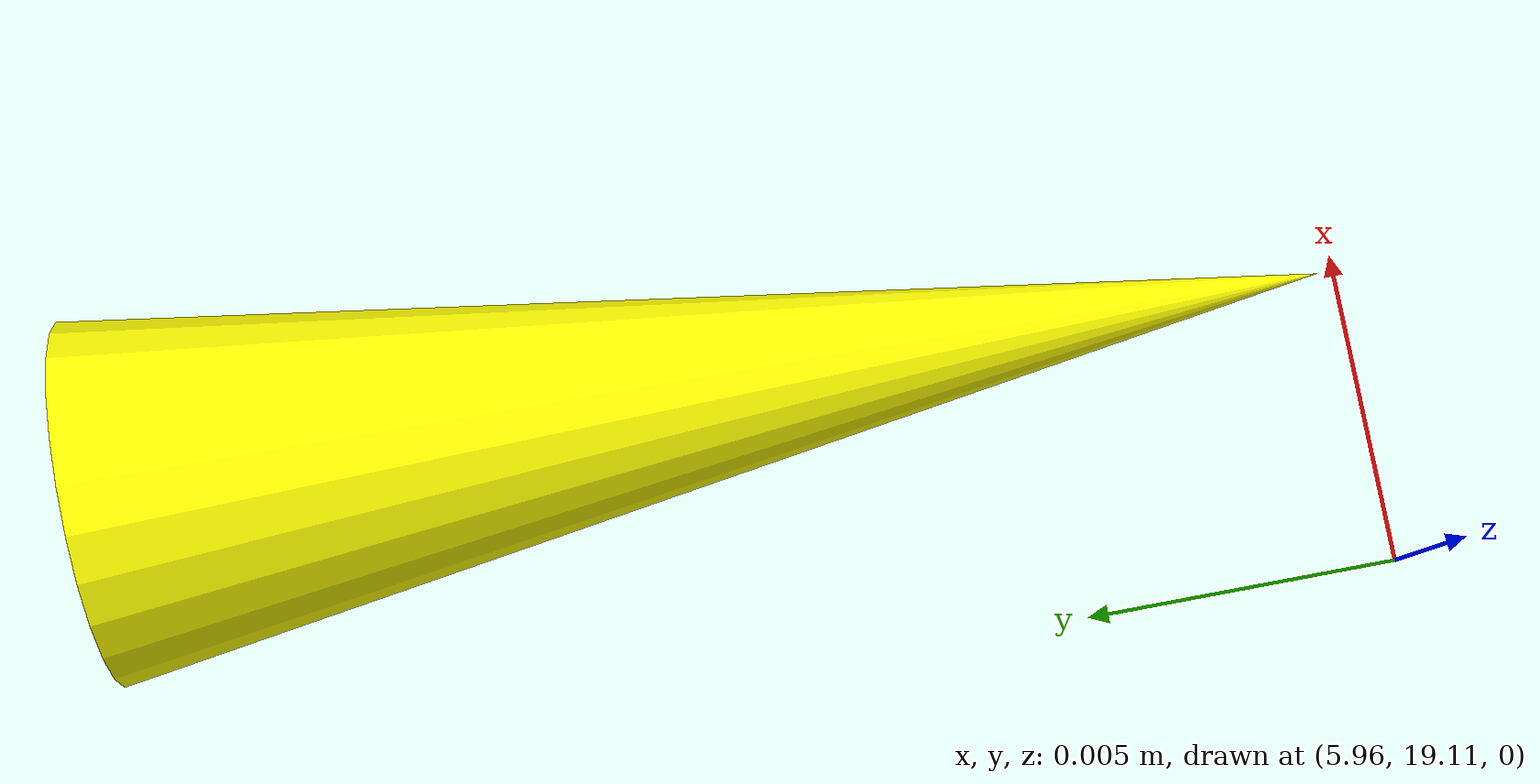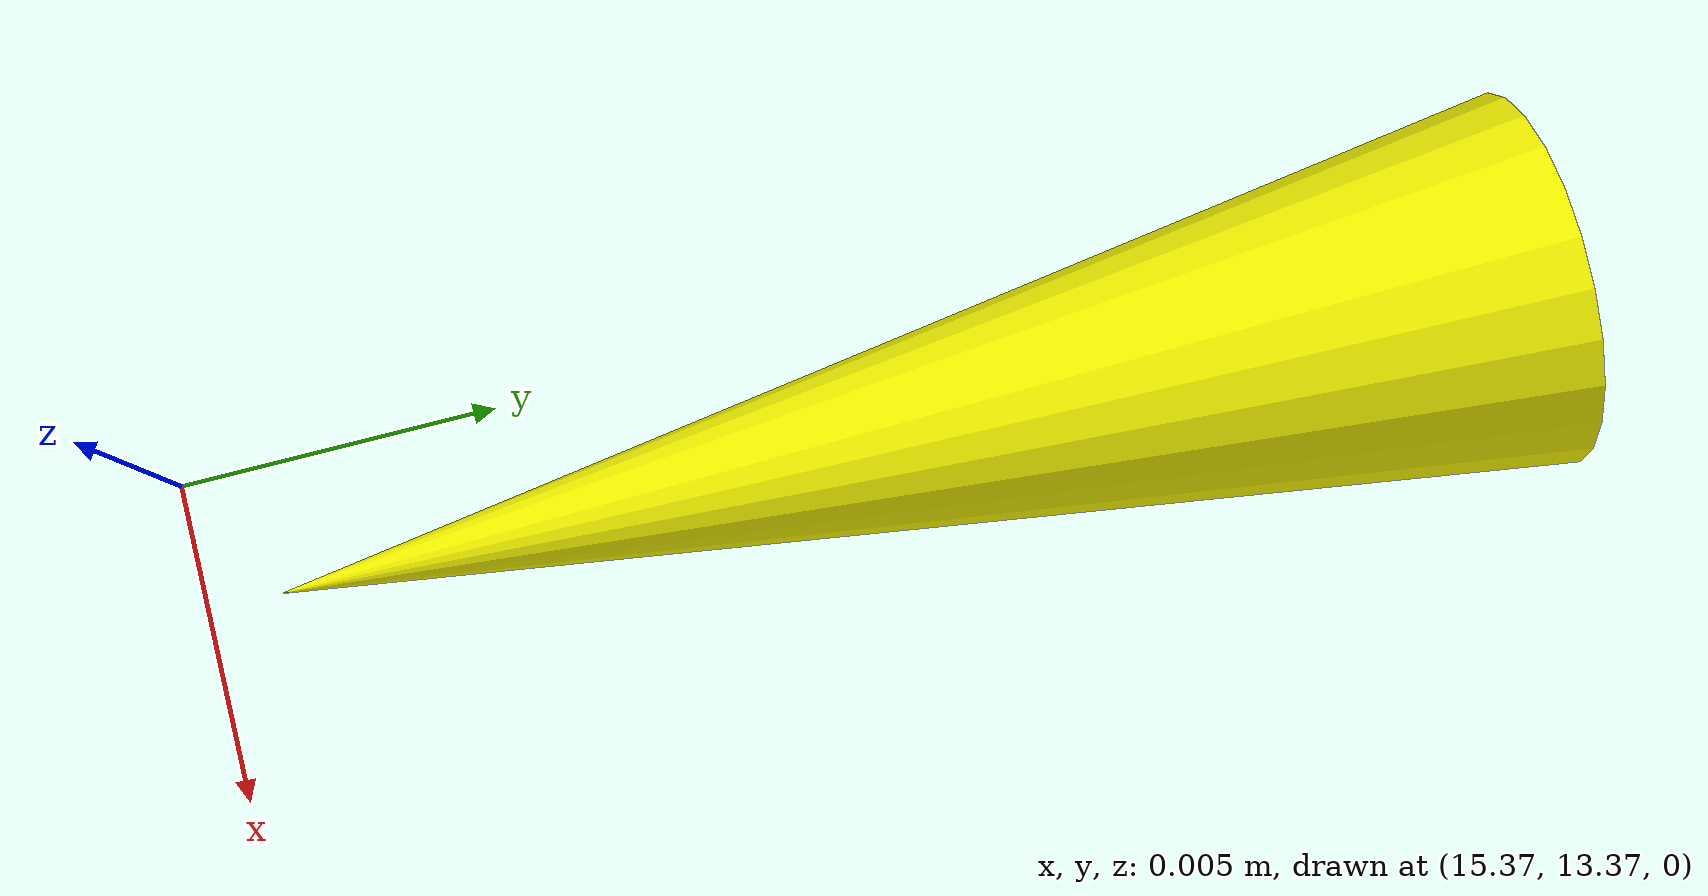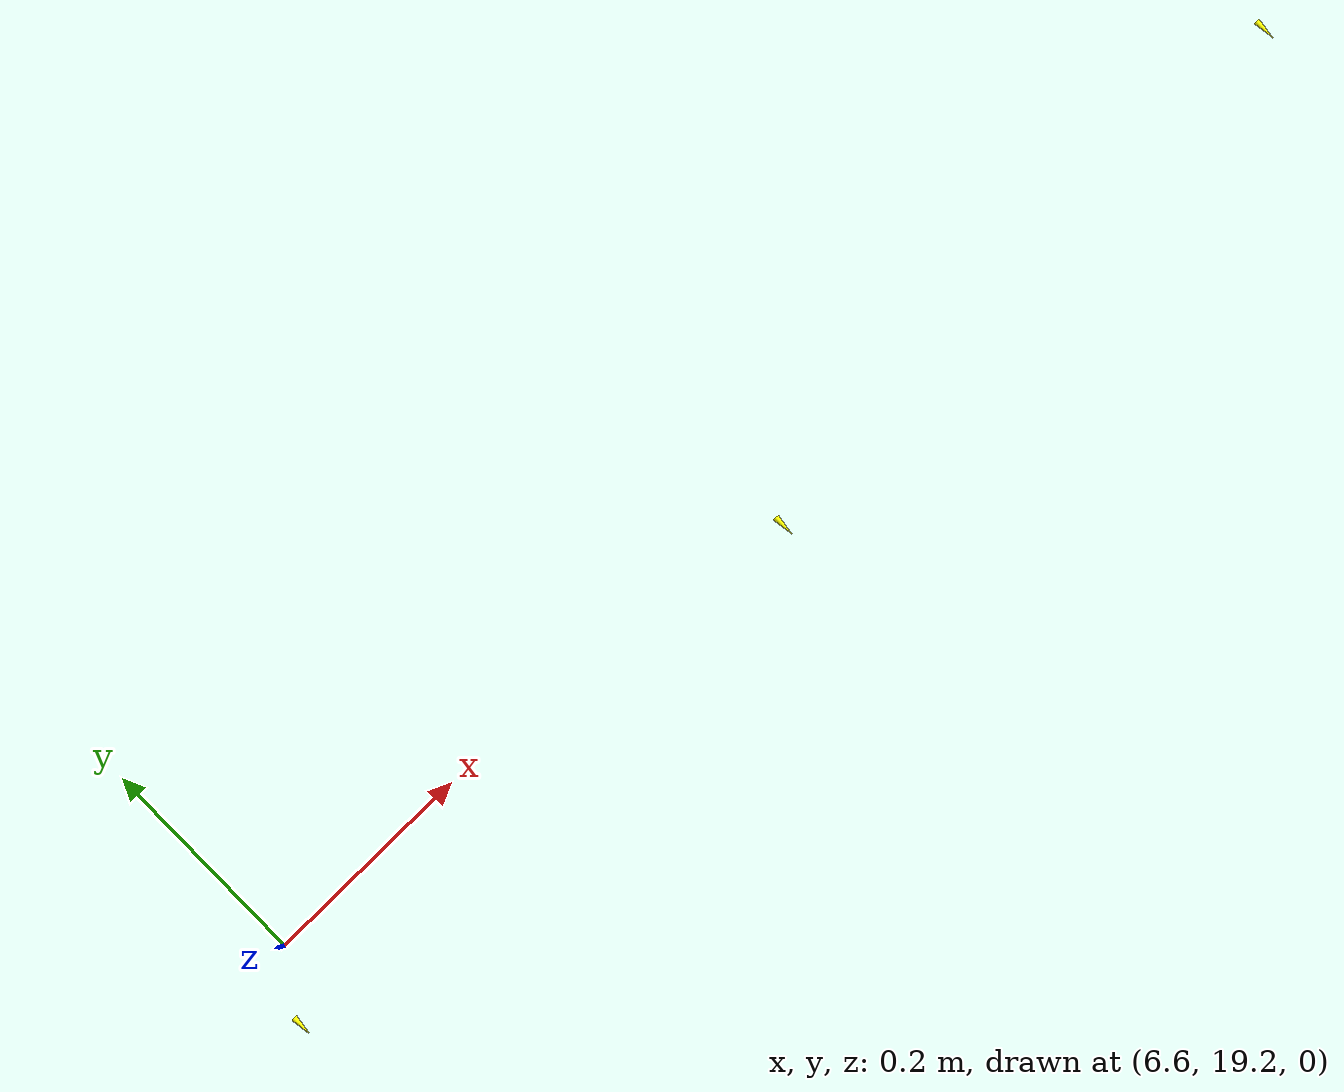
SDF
<?xml version="1.0"?>

<sdf version='1.9'>
<world name='track_yellow'>
     <model name='cone_0'>
      <link name='cone_0_link'>
        <inertial>
			<mass>0</mass>
			<inertia>
			<ixx>0.166667</ixx>
			<ixy>0</ixy>
			<ixz>0</ixz>
			<iyy>0.166667</iyy>
			<iyz>0</iyz>
			<izz>0.166667</izz>
			</inertia>
		</inertial>
        <collision name='cone_0_collision'>
          <geometry>
            <mesh>
              <uri>/models/cone/meshes/cone.stl</uri>
              <scale>0.001 0.001 0.001</scale>
            </mesh>
          </geometry>
        </collision>
        <visual name='cone_0_visual'>
          <geometry>
            <mesh>
              <uri>/models/cone/meshes/cone.stl</uri>
              <scale>0.001 0.001 0.001</scale>
            </mesh>
          </geometry>
          <material>
            <ambient>1 1 0 1</ambient>
            <diffuse>1 1 0 1</diffuse>
            <specular>1 1 0 1</specular>
          </material>
        </visual>

        <enable_wind>false</enable_wind>
      </link>
      <pose>5.365514631340422 19.110801933862014 0.0 1.57 0 0</pose>
      <static>true</static>
      </model>

     <model name='cone_1'>
      <link name='cone_1_link'>
        <inertial>
			<mass>0</mass>
			<inertia>
			<ixx>0.166667</ixx>
			<ixy>0</ixy>
			<ixz>0</ixz>
			<iyy>0.166667</iyy>
			<iyz>0</iyz>
			<izz>0.166667</izz>
			</inertia>
		</inertial>
        <collision name='cone_1_collision'>
          <geometry>
            <mesh>
              <uri>/models/cone/meshes/cone.stl</uri>
              <scale>0.001 0.001 0.001</scale>
            </mesh>
          </geometry>
        </collision>
        <visual name='cone_1_visual'>
          <geometry>
            <mesh>
              <uri>/models/cone/meshes/cone.stl</uri>
              <scale>0.001 0.001 0.001</scale>
            </mesh>
          </geometry>
          <material>
            <ambient>1 1 0 1</ambient>
            <diffuse>1 1 0 1</diffuse>
            <specular>1 1 0 1</specular>
          </material>
        </visual>

        <enable_wind>false</enable_wind>
      </link>
      <pose>5.964740565412263 19.13025210124988 0.0 1.57 0 0</pose>
      <static>true</static>
      </model>

     <model name='cone_2'>
      <link name='cone_2_link'>
        <inertial>
			<mass>0</mass>
			<inertia>
			<ixx>0.166667</ixx>
			<ixy>0</ixy>
			<ixz>0</ixz>
			<iyy>0.166667</iyy>
			<iyz>0</iyz>
			<izz>0.166667</izz>
			</inertia>
		</inertial>
        <collision name='cone_2_collision'>
          <geometry>
            <mesh>
              <uri>/models/cone/meshes/cone.stl</uri>
              <scale>0.001 0.001 0.001</scale>
            </mesh>
          </geometry>
        </collision>
        <visual name='cone_2_visual'>
          <geometry>
            <mesh>
              <uri>/models/cone/meshes/cone.stl</uri>
              <scale>0.001 0.001 0.001</scale>
            </mesh>
          </geometry>
          <material>
            <ambient>1 1 0 1</ambient>
            <diffuse>1 1 0 1</diffuse>
            <specular>1 1 0 1</specular>
          </material>
        </visual>

        <enable_wind>false</enable_wind>
      </link>
      <pose>6.562635671015661 19.149845757593543 0.0 1.57 0 0</pose>
      <static>true</static>
      </model>

     <model name='cone_3'>
      <link name='cone_3_link'>
        <inertial>
			<mass>0</mass>
			<inertia>
			<ixx>0.166667</ixx>
			<ixy>0</ixy>
			<ixz>0</ixz>
			<iyy>0.166667</iyy>
			<iyz>0</iyz>
			<izz>0.166667</izz>
			</inertia>
		</inertial>
        <collision name='cone_3_collision'>
          <geometry>
            <mesh>
              <uri>/models/cone/meshes/cone.stl</uri>
              <scale>0.001 0.001 0.001</scale>
            </mesh>
          </geometry>
        </collision>
        <visual name='cone_3_visual'>
          <geometry>
            <mesh>
              <uri>/models/cone/meshes/cone.stl</uri>
              <scale>0.001 0.001 0.001</scale>
            </mesh>
          </geometry>
          <material>
            <ambient>1 1 0 1</ambient>
            <diffuse>1 1 0 1</diffuse>
            <specular>1 1 0 1</specular>
          </material>
        </visual>

        <enable_wind>false</enable_wind>
      </link>
      <pose>7.159228228615251 19.168703466283013 0.0 1.57 0 0</pose>
      <static>true</static>
      </model>

     <model name='cone_4'>
      <link name='cone_4_link'>
        <inertial>
			<mass>0</mass>
			<inertia>
			<ixx>0.166667</ixx>
			<ixy>0</ixy>
			<ixz>0</ixz>
			<iyy>0.166667</iyy>
			<iyz>0</iyz>
			<izz>0.166667</izz>
			</inertia>
		</inertial>
        <collision name='cone_4_collision'>
          <geometry>
            <mesh>
              <uri>/models/cone/meshes/cone.stl</uri>
              <scale>0.001 0.001 0.001</scale>
            </mesh>
          </geometry>
        </collision>
        <visual name='cone_4_visual'>
          <geometry>
            <mesh>
              <uri>/models/cone/meshes/cone.stl</uri>
              <scale>0.001 0.001 0.001</scale>
            </mesh>
          </geometry>
          <material>
            <ambient>1 1 0 1</ambient>
            <diffuse>1 1 0 1</diffuse>
            <specular>1 1 0 1</specular>
          </material>
        </visual>

        <enable_wind>false</enable_wind>
      </link>
      <pose>7.754543277370971 19.185951549543113 0.0 1.57 0 0</pose>
      <static>true</static>
      </model>

     <model name='cone_5'>
      <link name='cone_5_link'>
        <inertial>
			<mass>0</mass>
			<inertia>
			<ixx>0.166667</ixx>
			<ixy>0</ixy>
			<ixz>0</ixz>
			<iyy>0.166667</iyy>
			<iyz>0</iyz>
			<izz>0.166667</izz>
			</inertia>
		</inertial>
        <collision name='cone_5_collision'>
          <geometry>
            <mesh>
              <uri>/models/cone/meshes/cone.stl</uri>
              <scale>0.001 0.001 0.001</scale>
            </mesh>
          </geometry>
        </collision>
        <visual name='cone_5_visual'>
          <geometry>
            <mesh>
              <uri>/models/cone/meshes/cone.stl</uri>
              <scale>0.001 0.001 0.001</scale>
            </mesh>
          </geometry>
          <material>
            <ambient>1 1 0 1</ambient>
            <diffuse>1 1 0 1</diffuse>
            <specular>1 1 0 1</specular>
          </material>
        </visual>

        <enable_wind>false</enable_wind>
      </link>
      <pose>8.348598776876031 19.20072199169762 0.0 1.57 0 0</pose>
      <static>true</static>
      </model>

     <model name='cone_6'>
      <link name='cone_6_link'>
        <inertial>
			<mass>0</mass>
			<inertia>
			<ixx>0.166667</ixx>
			<ixy>0</ixy>
			<ixz>0</ixz>
			<iyy>0.166667</iyy>
			<iyz>0</iyz>
			<izz>0.166667</izz>
			</inertia>
		</inertial>
        <collision name='cone_6_collision'>
          <geometry>
            <mesh>
              <uri>/models/cone/meshes/cone.stl</uri>
              <scale>0.001 0.001 0.001</scale>
            </mesh>
          </geometry>
        </collision>
        <visual name='cone_6_visual'>
          <geometry>
            <mesh>
              <uri>/models/cone/meshes/cone.stl</uri>
              <scale>0.001 0.001 0.001</scale>
            </mesh>
          </geometry>
          <material>
            <ambient>1 1 0 1</ambient>
            <diffuse>1 1 0 1</diffuse>
            <specular>1 1 0 1</specular>
          </material>
        </visual>

        <enable_wind>false</enable_wind>
      </link>
      <pose>10.12320195090182 19.22157188820107 0.0 1.57 0 0</pose>
      <static>true</static>
      </model>

     <model name='cone_7'>
      <link name='cone_7_link'>
        <inertial>
			<mass>0</mass>
			<inertia>
			<ixx>0.166667</ixx>
			<ixy>0</ixy>
			<ixz>0</ixz>
			<iyy>0.166667</iyy>
			<iyz>0</iyz>
			<izz>0.166667</izz>
			</inertia>
		</inertial>
        <collision name='cone_7_collision'>
          <geometry>
            <mesh>
              <uri>/models/cone/meshes/cone.stl</uri>
              <scale>0.001 0.001 0.001</scale>
            </mesh>
          </geometry>
        </collision>
        <visual name='cone_7_visual'>
          <geometry>
            <mesh>
              <uri>/models/cone/meshes/cone.stl</uri>
              <scale>0.001 0.001 0.001</scale>
            </mesh>
          </geometry>
          <material>
            <ambient>1 1 0 1</ambient>
            <diffuse>1 1 0 1</diffuse>
            <specular>1 1 0 1</specular>
          </material>
        </visual>

        <enable_wind>false</enable_wind>
      </link>
      <pose>10.71212526738323 19.21786514161583 0.0 1.57 0 0</pose>
      <static>true</static>
      </model>

     <model name='cone_8'>
      <link name='cone_8_link'>
        <inertial>
			<mass>0</mass>
			<inertia>
			<ixx>0.166667</ixx>
			<ixy>0</ixy>
			<ixz>0</ixz>
			<iyy>0.166667</iyy>
			<iyz>0</iyz>
			<izz>0.166667</izz>
			</inertia>
		</inertial>
        <collision name='cone_8_collision'>
          <geometry>
            <mesh>
              <uri>/models/cone/meshes/cone.stl</uri>
              <scale>0.001 0.001 0.001</scale>
            </mesh>
          </geometry>
        </collision>
        <visual name='cone_8_visual'>
          <geometry>
            <mesh>
              <uri>/models/cone/meshes/cone.stl</uri>
              <scale>0.001 0.001 0.001</scale>
            </mesh>
          </geometry>
          <material>
            <ambient>1 1 0 1</ambient>
            <diffuse>1 1 0 1</diffuse>
            <specular>1 1 0 1</specular>
          </material>
        </visual>

        <enable_wind>false</enable_wind>
      </link>
      <pose>11.299641250748362 19.20742738967495 0.0 1.57 0 0</pose>
      <static>true</static>
      </model>

     <model name='cone_9'>
      <link name='cone_9_link'>
        <inertial>
			<mass>0</mass>
			<inertia>
			<ixx>0.166667</ixx>
			<ixy>0</ixy>
			<ixz>0</ixz>
			<iyy>0.166667</iyy>
			<iyz>0</iyz>
			<izz>0.166667</izz>
			</inertia>
		</inertial>
        <collision name='cone_9_collision'>
          <geometry>
            <mesh>
              <uri>/models/cone/meshes/cone.stl</uri>
              <scale>0.001 0.001 0.001</scale>
            </mesh>
          </geometry>
        </collision>
        <visual name='cone_9_visual'>
          <geometry>
            <mesh>
              <uri>/models/cone/meshes/cone.stl</uri>
              <scale>0.001 0.001 0.001</scale>
            </mesh>
          </geometry>
          <material>
            <ambient>1 1 0 1</ambient>
            <diffuse>1 1 0 1</diffuse>
            <specular>1 1 0 1</specular>
          </material>
        </visual>

        <enable_wind>false</enable_wind>
      </link>
      <pose>11.88564717200543 19.189427374825613 0.0 1.57 0 0</pose>
      <static>true</static>
      </model>

     <model name='cone_10'>
      <link name='cone_10_link'>
        <inertial>
			<mass>0</mass>
			<inertia>
			<ixx>0.166667</ixx>
			<ixy>0</ixy>
			<ixz>0</ixz>
			<iyy>0.166667</iyy>
			<iyz>0</iyz>
			<izz>0.166667</izz>
			</inertia>
		</inertial>
        <collision name='cone_10_collision'>
          <geometry>
            <mesh>
              <uri>/models/cone/meshes/cone.stl</uri>
              <scale>0.001 0.001 0.001</scale>
            </mesh>
          </geometry>
        </collision>
        <visual name='cone_10_visual'>
          <geometry>
            <mesh>
              <uri>/models/cone/meshes/cone.stl</uri>
              <scale>0.001 0.001 0.001</scale>
            </mesh>
          </geometry>
          <material>
            <ambient>1 1 0 1</ambient>
            <diffuse>1 1 0 1</diffuse>
            <specular>1 1 0 1</specular>
          </material>
        </visual>

        <enable_wind>false</enable_wind>
      </link>
      <pose>12.47000759521337 19.16304179481803 0.0 1.57 0 0</pose>
      <static>true</static>
      </model>

     <model name='cone_11'>
      <link name='cone_11_link'>
        <inertial>
			<mass>0</mass>
			<inertia>
			<ixx>0.166667</ixx>
			<ixy>0</ixy>
			<ixz>0</ixz>
			<iyy>0.166667</iyy>
			<iyz>0</iyz>
			<izz>0.166667</izz>
			</inertia>
		</inertial>
        <collision name='cone_11_collision'>
          <geometry>
            <mesh>
              <uri>/models/cone/meshes/cone.stl</uri>
              <scale>0.001 0.001 0.001</scale>
            </mesh>
          </geometry>
        </collision>
        <visual name='cone_11_visual'>
          <geometry>
            <mesh>
              <uri>/models/cone/meshes/cone.stl</uri>
              <scale>0.001 0.001 0.001</scale>
            </mesh>
          </geometry>
          <material>
            <ambient>1 1 0 1</ambient>
            <diffuse>1 1 0 1</diffuse>
            <specular>1 1 0 1</specular>
          </material>
        </visual>

        <enable_wind>false</enable_wind>
      </link>
      <pose>13.041051502435192 19.12601093430245 0.0 1.57 0 0</pose>
      <static>true</static>
      </model>

     <model name='cone_12'>
      <link name='cone_12_link'>
        <inertial>
			<mass>0</mass>
			<inertia>
			<ixx>0.166667</ixx>
			<ixy>0</ixy>
			<ixz>0</ixz>
			<iyy>0.166667</iyy>
			<iyz>0</iyz>
			<izz>0.166667</izz>
			</inertia>
		</inertial>
        <collision name='cone_12_collision'>
          <geometry>
            <mesh>
              <uri>/models/cone/meshes/cone.stl</uri>
              <scale>0.001 0.001 0.001</scale>
            </mesh>
          </geometry>
        </collision>
        <visual name='cone_12_visual'>
          <geometry>
            <mesh>
              <uri>/models/cone/meshes/cone.stl</uri>
              <scale>0.001 0.001 0.001</scale>
            </mesh>
          </geometry>
          <material>
            <ambient>1 1 0 1</ambient>
            <diffuse>1 1 0 1</diffuse>
            <specular>1 1 0 1</specular>
          </material>
        </visual>

        <enable_wind>false</enable_wind>
      </link>
      <pose>13.581689096199652 19.06655367674996 0.0 1.57 0 0</pose>
      <static>true</static>
      </model>

     <model name='cone_13'>
      <link name='cone_13_link'>
        <inertial>
			<mass>0</mass>
			<inertia>
			<ixx>0.166667</ixx>
			<ixy>0</ixy>
			<ixz>0</ixz>
			<iyy>0.166667</iyy>
			<iyz>0</iyz>
			<izz>0.166667</izz>
			</inertia>
		</inertial>
        <collision name='cone_13_collision'>
          <geometry>
            <mesh>
              <uri>/models/cone/meshes/cone.stl</uri>
              <scale>0.001 0.001 0.001</scale>
            </mesh>
          </geometry>
        </collision>
        <visual name='cone_13_visual'>
          <geometry>
            <mesh>
              <uri>/models/cone/meshes/cone.stl</uri>
              <scale>0.001 0.001 0.001</scale>
            </mesh>
          </geometry>
          <material>
            <ambient>1 1 0 1</ambient>
            <diffuse>1 1 0 1</diffuse>
            <specular>1 1 0 1</specular>
          </material>
        </visual>

        <enable_wind>false</enable_wind>
      </link>
      <pose>14.55431448947459 18.83039695679588 0.0 1.57 0 0</pose>
      <static>true</static>
      </model>

     <model name='cone_14'>
      <link name='cone_14_link'>
        <inertial>
			<mass>0</mass>
			<inertia>
			<ixx>0.166667</ixx>
			<ixy>0</ixy>
			<ixz>0</ixz>
			<iyy>0.166667</iyy>
			<iyz>0</iyz>
			<izz>0.166667</izz>
			</inertia>
		</inertial>
        <collision name='cone_14_collision'>
          <geometry>
            <mesh>
              <uri>/models/cone/meshes/cone.stl</uri>
              <scale>0.001 0.001 0.001</scale>
            </mesh>
          </geometry>
        </collision>
        <visual name='cone_14_visual'>
          <geometry>
            <mesh>
              <uri>/models/cone/meshes/cone.stl</uri>
              <scale>0.001 0.001 0.001</scale>
            </mesh>
          </geometry>
          <material>
            <ambient>1 1 0 1</ambient>
            <diffuse>1 1 0 1</diffuse>
            <specular>1 1 0 1</specular>
          </material>
        </visual>

        <enable_wind>false</enable_wind>
      </link>
      <pose>14.97041312626016 18.63808357122464 0.0 1.57 0 0</pose>
      <static>true</static>
      </model>

     <model name='cone_15'>
      <link name='cone_15_link'>
        <inertial>
			<mass>0</mass>
			<inertia>
			<ixx>0.166667</ixx>
			<ixy>0</ixy>
			<ixz>0</ixz>
			<iyy>0.166667</iyy>
			<iyz>0</iyz>
			<izz>0.166667</izz>
			</inertia>
		</inertial>
        <collision name='cone_15_collision'>
          <geometry>
            <mesh>
              <uri>/models/cone/meshes/cone.stl</uri>
              <scale>0.001 0.001 0.001</scale>
            </mesh>
          </geometry>
        </collision>
        <visual name='cone_15_visual'>
          <geometry>
            <mesh>
              <uri>/models/cone/meshes/cone.stl</uri>
              <scale>0.001 0.001 0.001</scale>
            </mesh>
          </geometry>
          <material>
            <ambient>1 1 0 1</ambient>
            <diffuse>1 1 0 1</diffuse>
            <specular>1 1 0 1</specular>
          </material>
        </visual>

        <enable_wind>false</enable_wind>
      </link>
      <pose>15.64211758381664 18.078554715443932 0.0 1.57 0 0</pose>
      <static>true</static>
      </model>

     <model name='cone_16'>
      <link name='cone_16_link'>
        <inertial>
			<mass>0</mass>
			<inertia>
			<ixx>0.166667</ixx>
			<ixy>0</ixy>
			<ixz>0</ixz>
			<iyy>0.166667</iyy>
			<iyz>0</iyz>
			<izz>0.166667</izz>
			</inertia>
		</inertial>
        <collision name='cone_16_collision'>
          <geometry>
            <mesh>
              <uri>/models/cone/meshes/cone.stl</uri>
              <scale>0.001 0.001 0.001</scale>
            </mesh>
          </geometry>
        </collision>
        <visual name='cone_16_visual'>
          <geometry>
            <mesh>
              <uri>/models/cone/meshes/cone.stl</uri>
              <scale>0.001 0.001 0.001</scale>
            </mesh>
          </geometry>
          <material>
            <ambient>1 1 0 1</ambient>
            <diffuse>1 1 0 1</diffuse>
            <specular>1 1 0 1</specular>
          </material>
        </visual>

        <enable_wind>false</enable_wind>
      </link>
      <pose>15.910013498130139 17.706310771870402 0.0 1.57 0 0</pose>
      <static>true</static>
      </model>

     <model name='cone_17'>
      <link name='cone_17_link'>
        <inertial>
			<mass>0</mass>
			<inertia>
			<ixx>0.166667</ixx>
			<ixy>0</ixy>
			<ixz>0</ixz>
			<iyy>0.166667</iyy>
			<iyz>0</iyz>
			<izz>0.166667</izz>
			</inertia>
		</inertial>
        <collision name='cone_17_collision'>
          <geometry>
            <mesh>
              <uri>/models/cone/meshes/cone.stl</uri>
              <scale>0.001 0.001 0.001</scale>
            </mesh>
          </geometry>
        </collision>
        <visual name='cone_17_visual'>
          <geometry>
            <mesh>
              <uri>/models/cone/meshes/cone.stl</uri>
              <scale>0.001 0.001 0.001</scale>
            </mesh>
          </geometry>
          <material>
            <ambient>1 1 0 1</ambient>
            <diffuse>1 1 0 1</diffuse>
            <specular>1 1 0 1</specular>
          </material>
        </visual>

        <enable_wind>false</enable_wind>
      </link>
      <pose>16.1277216977834 17.285362386631014 0.0 1.57 0 0</pose>
      <static>true</static>
      </model>

     <model name='cone_18'>
      <link name='cone_18_link'>
        <inertial>
			<mass>0</mass>
			<inertia>
			<ixx>0.166667</ixx>
			<ixy>0</ixy>
			<ixz>0</ixz>
			<iyy>0.166667</iyy>
			<iyz>0</iyz>
			<izz>0.166667</izz>
			</inertia>
		</inertial>
        <collision name='cone_18_collision'>
          <geometry>
            <mesh>
              <uri>/models/cone/meshes/cone.stl</uri>
              <scale>0.001 0.001 0.001</scale>
            </mesh>
          </geometry>
        </collision>
        <visual name='cone_18_visual'>
          <geometry>
            <mesh>
              <uri>/models/cone/meshes/cone.stl</uri>
              <scale>0.001 0.001 0.001</scale>
            </mesh>
          </geometry>
          <material>
            <ambient>1 1 0 1</ambient>
            <diffuse>1 1 0 1</diffuse>
            <specular>1 1 0 1</specular>
          </material>
        </visual>

        <enable_wind>false</enable_wind>
      </link>
      <pose>16.294295500331152 16.825754413038084 0.0 1.57 0 0</pose>
      <static>true</static>
      </model>

     <model name='cone_19'>
      <link name='cone_19_link'>
        <inertial>
			<mass>0</mass>
			<inertia>
			<ixx>0.166667</ixx>
			<ixy>0</ixy>
			<ixz>0</ixz>
			<iyy>0.166667</iyy>
			<iyz>0</iyz>
			<izz>0.166667</izz>
			</inertia>
		</inertial>
        <collision name='cone_19_collision'>
          <geometry>
            <mesh>
              <uri>/models/cone/meshes/cone.stl</uri>
              <scale>0.001 0.001 0.001</scale>
            </mesh>
          </geometry>
        </collision>
        <visual name='cone_19_visual'>
          <geometry>
            <mesh>
              <uri>/models/cone/meshes/cone.stl</uri>
              <scale>0.001 0.001 0.001</scale>
            </mesh>
          </geometry>
          <material>
            <ambient>1 1 0 1</ambient>
            <diffuse>1 1 0 1</diffuse>
            <specular>1 1 0 1</specular>
          </material>
        </visual>

        <enable_wind>false</enable_wind>
      </link>
      <pose>16.45404444091331 15.871680009410992 0.0 1.57 0 0</pose>
      <static>true</static>
      </model>

     <model name='cone_20'>
      <link name='cone_20_link'>
        <inertial>
			<mass>0</mass>
			<inertia>
			<ixx>0.166667</ixx>
			<ixy>0</ixy>
			<ixz>0</ixz>
			<iyy>0.166667</iyy>
			<iyz>0</iyz>
			<izz>0.166667</izz>
			</inertia>
		</inertial>
        <collision name='cone_20_collision'>
          <geometry>
            <mesh>
              <uri>/models/cone/meshes/cone.stl</uri>
              <scale>0.001 0.001 0.001</scale>
            </mesh>
          </geometry>
        </collision>
        <visual name='cone_20_visual'>
          <geometry>
            <mesh>
              <uri>/models/cone/meshes/cone.stl</uri>
              <scale>0.001 0.001 0.001</scale>
            </mesh>
          </geometry>
          <material>
            <ambient>1 1 0 1</ambient>
            <diffuse>1 1 0 1</diffuse>
            <specular>1 1 0 1</specular>
          </material>
        </visual>

        <enable_wind>false</enable_wind>
      </link>
      <pose>16.43842788566033 15.399601279681972 0.0 1.57 0 0</pose>
      <static>true</static>
      </model>

     <model name='cone_21'>
      <link name='cone_21_link'>
        <inertial>
			<mass>0</mass>
			<inertia>
			<ixx>0.166667</ixx>
			<ixy>0</ixy>
			<ixz>0</ixz>
			<iyy>0.166667</iyy>
			<iyz>0</iyz>
			<izz>0.166667</izz>
			</inertia>
		</inertial>
        <collision name='cone_21_collision'>
          <geometry>
            <mesh>
              <uri>/models/cone/meshes/cone.stl</uri>
              <scale>0.001 0.001 0.001</scale>
            </mesh>
          </geometry>
        </collision>
        <visual name='cone_21_visual'>
          <geometry>
            <mesh>
              <uri>/models/cone/meshes/cone.stl</uri>
              <scale>0.001 0.001 0.001</scale>
            </mesh>
          </geometry>
          <material>
            <ambient>1 1 0 1</ambient>
            <diffuse>1 1 0 1</diffuse>
            <specular>1 1 0 1</specular>
          </material>
        </visual>

        <enable_wind>false</enable_wind>
      </link>
      <pose>16.356500140432672 14.942758602394552 0.0 1.57 0 0</pose>
      <static>true</static>
      </model>

     <model name='cone_22'>
      <link name='cone_22_link'>
        <inertial>
			<mass>0</mass>
			<inertia>
			<ixx>0.166667</ixx>
			<ixy>0</ixy>
			<ixz>0</ixz>
			<iyy>0.166667</iyy>
			<iyz>0</iyz>
			<izz>0.166667</izz>
			</inertia>
		</inertial>
        <collision name='cone_22_collision'>
          <geometry>
            <mesh>
              <uri>/models/cone/meshes/cone.stl</uri>
              <scale>0.001 0.001 0.001</scale>
            </mesh>
          </geometry>
        </collision>
        <visual name='cone_22_visual'>
          <geometry>
            <mesh>
              <uri>/models/cone/meshes/cone.stl</uri>
              <scale>0.001 0.001 0.001</scale>
            </mesh>
          </geometry>
          <material>
            <ambient>1 1 0 1</ambient>
            <diffuse>1 1 0 1</diffuse>
            <specular>1 1 0 1</specular>
          </material>
        </visual>

        <enable_wind>false</enable_wind>
      </link>
      <pose>16.20837454523762 14.511568577870843 0.0 1.57 0 0</pose>
      <static>true</static>
      </model>

     <model name='cone_23'>
      <link name='cone_23_link'>
        <inertial>
			<mass>0</mass>
			<inertia>
			<ixx>0.166667</ixx>
			<ixy>0</ixy>
			<ixz>0</ixz>
			<iyy>0.166667</iyy>
			<iyz>0</iyz>
			<izz>0.166667</izz>
			</inertia>
		</inertial>
        <collision name='cone_23_collision'>
          <geometry>
            <mesh>
              <uri>/models/cone/meshes/cone.stl</uri>
              <scale>0.001 0.001 0.001</scale>
            </mesh>
          </geometry>
        </collision>
        <visual name='cone_23_visual'>
          <geometry>
            <mesh>
              <uri>/models/cone/meshes/cone.stl</uri>
              <scale>0.001 0.001 0.001</scale>
            </mesh>
          </geometry>
          <material>
            <ambient>1 1 0 1</ambient>
            <diffuse>1 1 0 1</diffuse>
            <specular>1 1 0 1</specular>
          </material>
        </visual>

        <enable_wind>false</enable_wind>
      </link>
      <pose>15.99358132323365 14.11083754486181 0.0 1.57 0 0</pose>
      <static>true</static>
      </model>

     <model name='cone_24'>
      <link name='cone_24_link'>
        <inertial>
			<mass>0</mass>
			<inertia>
			<ixx>0.166667</ixx>
			<ixy>0</ixy>
			<ixz>0</ixz>
			<iyy>0.166667</iyy>
			<iyz>0</iyz>
			<izz>0.166667</izz>
			</inertia>
		</inertial>
        <collision name='cone_24_collision'>
          <geometry>
            <mesh>
              <uri>/models/cone/meshes/cone.stl</uri>
              <scale>0.001 0.001 0.001</scale>
            </mesh>
          </geometry>
        </collision>
        <visual name='cone_24_visual'>
          <geometry>
            <mesh>
              <uri>/models/cone/meshes/cone.stl</uri>
              <scale>0.001 0.001 0.001</scale>
            </mesh>
          </geometry>
          <material>
            <ambient>1 1 0 1</ambient>
            <diffuse>1 1 0 1</diffuse>
            <specular>1 1 0 1</specular>
          </material>
        </visual>

        <enable_wind>false</enable_wind>
      </link>
      <pose>15.371974790252331 13.391132889904732 0.0 1.57 0 0</pose>
      <static>true</static>
      </model>

     <model name='cone_25'>
      <link name='cone_25_link'>
        <inertial>
			<mass>0</mass>
			<inertia>
			<ixx>0.166667</ixx>
			<ixy>0</ixy>
			<ixz>0</ixz>
			<iyy>0.166667</iyy>
			<iyz>0</iyz>
			<izz>0.166667</izz>
			</inertia>
		</inertial>
        <collision name='cone_25_collision'>
          <geometry>
            <mesh>
              <uri>/models/cone/meshes/cone.stl</uri>
              <scale>0.001 0.001 0.001</scale>
            </mesh>
          </geometry>
        </collision>
        <visual name='cone_25_visual'>
          <geometry>
            <mesh>
              <uri>/models/cone/meshes/cone.stl</uri>
              <scale>0.001 0.001 0.001</scale>
            </mesh>
          </geometry>
          <material>
            <ambient>1 1 0 1</ambient>
            <diffuse>1 1 0 1</diffuse>
            <specular>1 1 0 1</specular>
          </material>
        </visual>

        <enable_wind>false</enable_wind>
      </link>
      <pose>14.55709628279117 12.808898370122453 0.0 1.57 0 0</pose>
      <static>true</static>
      </model>

     <model name='cone_26'>
      <link name='cone_26_link'>
        <inertial>
			<mass>0</mass>
			<inertia>
			<ixx>0.166667</ixx>
			<ixy>0</ixy>
			<ixz>0</ixz>
			<iyy>0.166667</iyy>
			<iyz>0</iyz>
			<izz>0.166667</izz>
			</inertia>
		</inertial>
        <collision name='cone_26_collision'>
          <geometry>
            <mesh>
              <uri>/models/cone/meshes/cone.stl</uri>
              <scale>0.001 0.001 0.001</scale>
            </mesh>
          </geometry>
        </collision>
        <visual name='cone_26_visual'>
          <geometry>
            <mesh>
              <uri>/models/cone/meshes/cone.stl</uri>
              <scale>0.001 0.001 0.001</scale>
            </mesh>
          </geometry>
          <material>
            <ambient>1 1 0 1</ambient>
            <diffuse>1 1 0 1</diffuse>
            <specular>1 1 0 1</specular>
          </material>
        </visual>

        <enable_wind>false</enable_wind>
      </link>
      <pose>14.11033563835196 12.587555216181531 0.0 1.57 0 0</pose>
      <static>true</static>
      </model>

     <model name='cone_27'>
      <link name='cone_27_link'>
        <inertial>
			<mass>0</mass>
			<inertia>
			<ixx>0.166667</ixx>
			<ixy>0</ixy>
			<ixz>0</ixz>
			<iyy>0.166667</iyy>
			<iyz>0</iyz>
			<izz>0.166667</izz>
			</inertia>
		</inertial>
        <collision name='cone_27_collision'>
          <geometry>
            <mesh>
              <uri>/models/cone/meshes/cone.stl</uri>
              <scale>0.001 0.001 0.001</scale>
            </mesh>
          </geometry>
        </collision>
        <visual name='cone_27_visual'>
          <geometry>
            <mesh>
              <uri>/models/cone/meshes/cone.stl</uri>
              <scale>0.001 0.001 0.001</scale>
            </mesh>
          </geometry>
          <material>
            <ambient>1 1 0 1</ambient>
            <diffuse>1 1 0 1</diffuse>
            <specular>1 1 0 1</specular>
          </material>
        </visual>

        <enable_wind>false</enable_wind>
      </link>
      <pose>13.646279059230352 12.420128168078872 0.0 1.57 0 0</pose>
      <static>true</static>
      </model>

     <model name='cone_28'>
      <link name='cone_28_link'>
        <inertial>
			<mass>0</mass>
			<inertia>
			<ixx>0.166667</ixx>
			<ixy>0</ixy>
			<ixz>0</ixz>
			<iyy>0.166667</iyy>
			<iyz>0</iyz>
			<izz>0.166667</izz>
			</inertia>
		</inertial>
        <collision name='cone_28_collision'>
          <geometry>
            <mesh>
              <uri>/models/cone/meshes/cone.stl</uri>
              <scale>0.001 0.001 0.001</scale>
            </mesh>
          </geometry>
        </collision>
        <visual name='cone_28_visual'>
          <geometry>
            <mesh>
              <uri>/models/cone/meshes/cone.stl</uri>
              <scale>0.001 0.001 0.001</scale>
            </mesh>
          </geometry>
          <material>
            <ambient>1 1 0 1</ambient>
            <diffuse>1 1 0 1</diffuse>
            <specular>1 1 0 1</specular>
          </material>
        </visual>

        <enable_wind>false</enable_wind>
      </link>
      <pose>13.17068350719518 12.310419448693313 0.0 1.57 0 0</pose>
      <static>true</static>
      </model>

     <model name='cone_29'>
      <link name='cone_29_link'>
        <inertial>
			<mass>0</mass>
			<inertia>
			<ixx>0.166667</ixx>
			<ixy>0</ixy>
			<ixz>0</ixz>
			<iyy>0.166667</iyy>
			<iyz>0</iyz>
			<izz>0.166667</izz>
			</inertia>
		</inertial>
        <collision name='cone_29_collision'>
          <geometry>
            <mesh>
              <uri>/models/cone/meshes/cone.stl</uri>
              <scale>0.001 0.001 0.001</scale>
            </mesh>
          </geometry>
        </collision>
        <visual name='cone_29_visual'>
          <geometry>
            <mesh>
              <uri>/models/cone/meshes/cone.stl</uri>
              <scale>0.001 0.001 0.001</scale>
            </mesh>
          </geometry>
          <material>
            <ambient>1 1 0 1</ambient>
            <diffuse>1 1 0 1</diffuse>
            <specular>1 1 0 1</specular>
          </material>
        </visual>

        <enable_wind>false</enable_wind>
      </link>
      <pose>12.69032803057931 12.261562816865302 0.0 1.57 0 0</pose>
      <static>true</static>
      </model>

     <model name='cone_30'>
      <link name='cone_30_link'>
        <inertial>
			<mass>0</mass>
			<inertia>
			<ixx>0.166667</ixx>
			<ixy>0</ixy>
			<ixz>0</ixz>
			<iyy>0.166667</iyy>
			<iyz>0</iyz>
			<izz>0.166667</izz>
			</inertia>
		</inertial>
        <collision name='cone_30_collision'>
          <geometry>
            <mesh>
              <uri>/models/cone/meshes/cone.stl</uri>
              <scale>0.001 0.001 0.001</scale>
            </mesh>
          </geometry>
        </collision>
        <visual name='cone_30_visual'>
          <geometry>
            <mesh>
              <uri>/models/cone/meshes/cone.stl</uri>
              <scale>0.001 0.001 0.001</scale>
            </mesh>
          </geometry>
          <material>
            <ambient>1 1 0 1</ambient>
            <diffuse>1 1 0 1</diffuse>
            <specular>1 1 0 1</specular>
          </material>
        </visual>

        <enable_wind>false</enable_wind>
      </link>
      <pose>12.20867904572405 12.275499276402233 0.0 1.57 0 0</pose>
      <static>true</static>
      </model>

     <model name='cone_31'>
      <link name='cone_31_link'>
        <inertial>
			<mass>0</mass>
			<inertia>
			<ixx>0.166667</ixx>
			<ixy>0</ixy>
			<ixz>0</ixz>
			<iyy>0.166667</iyy>
			<iyz>0</iyz>
			<izz>0.166667</izz>
			</inertia>
		</inertial>
        <collision name='cone_31_collision'>
          <geometry>
            <mesh>
              <uri>/models/cone/meshes/cone.stl</uri>
              <scale>0.001 0.001 0.001</scale>
            </mesh>
          </geometry>
        </collision>
        <visual name='cone_31_visual'>
          <geometry>
            <mesh>
              <uri>/models/cone/meshes/cone.stl</uri>
              <scale>0.001 0.001 0.001</scale>
            </mesh>
          </geometry>
          <material>
            <ambient>1 1 0 1</ambient>
            <diffuse>1 1 0 1</diffuse>
            <specular>1 1 0 1</specular>
          </material>
        </visual>

        <enable_wind>false</enable_wind>
      </link>
      <pose>11.722728008294931 12.350486889681113 0.0 1.57 0 0</pose>
      <static>true</static>
      </model>

     <model name='cone_32'>
      <link name='cone_32_link'>
        <inertial>
			<mass>0</mass>
			<inertia>
			<ixx>0.166667</ixx>
			<ixy>0</ixy>
			<ixz>0</ixz>
			<iyy>0.166667</iyy>
			<iyz>0</iyz>
			<izz>0.166667</izz>
			</inertia>
		</inertial>
        <collision name='cone_32_collision'>
          <geometry>
            <mesh>
              <uri>/models/cone/meshes/cone.stl</uri>
              <scale>0.001 0.001 0.001</scale>
            </mesh>
          </geometry>
        </collision>
        <visual name='cone_32_visual'>
          <geometry>
            <mesh>
              <uri>/models/cone/meshes/cone.stl</uri>
              <scale>0.001 0.001 0.001</scale>
            </mesh>
          </geometry>
          <material>
            <ambient>1 1 0 1</ambient>
            <diffuse>1 1 0 1</diffuse>
            <specular>1 1 0 1</specular>
          </material>
        </visual>

        <enable_wind>false</enable_wind>
      </link>
      <pose>10.75994651673809 12.66625218214823 0.0 1.57 0 0</pose>
      <static>true</static>
      </model>

     <model name='cone_33'>
      <link name='cone_33_link'>
        <inertial>
			<mass>0</mass>
			<inertia>
			<ixx>0.166667</ixx>
			<ixy>0</ixy>
			<ixz>0</ixz>
			<iyy>0.166667</iyy>
			<iyz>0</iyz>
			<izz>0.166667</izz>
			</inertia>
		</inertial>
        <collision name='cone_33_collision'>
          <geometry>
            <mesh>
              <uri>/models/cone/meshes/cone.stl</uri>
              <scale>0.001 0.001 0.001</scale>
            </mesh>
          </geometry>
        </collision>
        <visual name='cone_33_visual'>
          <geometry>
            <mesh>
              <uri>/models/cone/meshes/cone.stl</uri>
              <scale>0.001 0.001 0.001</scale>
            </mesh>
          </geometry>
          <material>
            <ambient>1 1 0 1</ambient>
            <diffuse>1 1 0 1</diffuse>
            <specular>1 1 0 1</specular>
          </material>
        </visual>

        <enable_wind>false</enable_wind>
      </link>
      <pose>9.827743761109641 13.170460850358321 0.0 1.57 0 0</pose>
      <static>true</static>
      </model>

     <model name='cone_34'>
      <link name='cone_34_link'>
        <inertial>
			<mass>0</mass>
			<inertia>
			<ixx>0.166667</ixx>
			<ixy>0</ixy>
			<ixz>0</ixz>
			<iyy>0.166667</iyy>
			<iyz>0</iyz>
			<izz>0.166667</izz>
			</inertia>
		</inertial>
        <collision name='cone_34_collision'>
          <geometry>
            <mesh>
              <uri>/models/cone/meshes/cone.stl</uri>
              <scale>0.001 0.001 0.001</scale>
            </mesh>
          </geometry>
        </collision>
        <visual name='cone_34_visual'>
          <geometry>
            <mesh>
              <uri>/models/cone/meshes/cone.stl</uri>
              <scale>0.001 0.001 0.001</scale>
            </mesh>
          </geometry>
          <material>
            <ambient>1 1 0 1</ambient>
            <diffuse>1 1 0 1</diffuse>
            <specular>1 1 0 1</specular>
          </material>
        </visual>

        <enable_wind>false</enable_wind>
      </link>
      <pose>9.359338739919142 13.482384021496312 0.0 1.57 0 0</pose>
      <static>true</static>
      </model>

     <model name='cone_35'>
      <link name='cone_35_link'>
        <inertial>
			<mass>0</mass>
			<inertia>
			<ixx>0.166667</ixx>
			<ixy>0</ixy>
			<ixz>0</ixz>
			<iyy>0.166667</iyy>
			<iyz>0</iyz>
			<izz>0.166667</izz>
			</inertia>
		</inertial>
        <collision name='cone_35_collision'>
          <geometry>
            <mesh>
              <uri>/models/cone/meshes/cone.stl</uri>
              <scale>0.001 0.001 0.001</scale>
            </mesh>
          </geometry>
        </collision>
        <visual name='cone_35_visual'>
          <geometry>
            <mesh>
              <uri>/models/cone/meshes/cone.stl</uri>
              <scale>0.001 0.001 0.001</scale>
            </mesh>
          </geometry>
          <material>
            <ambient>1 1 0 1</ambient>
            <diffuse>1 1 0 1</diffuse>
            <specular>1 1 0 1</specular>
          </material>
        </visual>

        <enable_wind>false</enable_wind>
      </link>
      <pose>8.87839159937207 13.820768859629933 0.0 1.57 0 0</pose>
      <static>true</static>
      </model>

     <model name='cone_36'>
      <link name='cone_36_link'>
        <inertial>
			<mass>0</mass>
			<inertia>
			<ixx>0.166667</ixx>
			<ixy>0</ixy>
			<ixz>0</ixz>
			<iyy>0.166667</iyy>
			<iyz>0</iyz>
			<izz>0.166667</izz>
			</inertia>
		</inertial>
        <collision name='cone_36_collision'>
          <geometry>
            <mesh>
              <uri>/models/cone/meshes/cone.stl</uri>
              <scale>0.001 0.001 0.001</scale>
            </mesh>
          </geometry>
        </collision>
        <visual name='cone_36_visual'>
          <geometry>
            <mesh>
              <uri>/models/cone/meshes/cone.stl</uri>
              <scale>0.001 0.001 0.001</scale>
            </mesh>
          </geometry>
          <material>
            <ambient>1 1 0 1</ambient>
            <diffuse>1 1 0 1</diffuse>
            <specular>1 1 0 1</specular>
          </material>
        </visual>

        <enable_wind>false</enable_wind>
      </link>
      <pose>8.37592777156742 14.172470621296402 0.0 1.57 0 0</pose>
      <static>true</static>
      </model>

     <model name='cone_37'>
      <link name='cone_37_link'>
        <inertial>
			<mass>0</mass>
			<inertia>
			<ixx>0.166667</ixx>
			<ixy>0</ixy>
			<ixz>0</ixz>
			<iyy>0.166667</iyy>
			<iyz>0</iyz>
			<izz>0.166667</izz>
			</inertia>
		</inertial>
        <collision name='cone_37_collision'>
          <geometry>
            <mesh>
              <uri>/models/cone/meshes/cone.stl</uri>
              <scale>0.001 0.001 0.001</scale>
            </mesh>
          </geometry>
        </collision>
        <visual name='cone_37_visual'>
          <geometry>
            <mesh>
              <uri>/models/cone/meshes/cone.stl</uri>
              <scale>0.001 0.001 0.001</scale>
            </mesh>
          </geometry>
          <material>
            <ambient>1 1 0 1</ambient>
            <diffuse>1 1 0 1</diffuse>
            <specular>1 1 0 1</specular>
          </material>
        </visual>

        <enable_wind>false</enable_wind>
      </link>
      <pose>7.841881389339381 14.522514218116822 0.0 1.57 0 0</pose>
      <static>true</static>
      </model>

     <model name='cone_38'>
      <link name='cone_38_link'>
        <inertial>
			<mass>0</mass>
			<inertia>
			<ixx>0.166667</ixx>
			<ixy>0</ixy>
			<ixz>0</ixz>
			<iyy>0.166667</iyy>
			<iyz>0</iyz>
			<izz>0.166667</izz>
			</inertia>
		</inertial>
        <collision name='cone_38_collision'>
          <geometry>
            <mesh>
              <uri>/models/cone/meshes/cone.stl</uri>
              <scale>0.001 0.001 0.001</scale>
            </mesh>
          </geometry>
        </collision>
        <visual name='cone_38_visual'>
          <geometry>
            <mesh>
              <uri>/models/cone/meshes/cone.stl</uri>
              <scale>0.001 0.001 0.001</scale>
            </mesh>
          </geometry>
          <material>
            <ambient>1 1 0 1</ambient>
            <diffuse>1 1 0 1</diffuse>
            <specular>1 1 0 1</specular>
          </material>
        </visual>

        <enable_wind>false</enable_wind>
      </link>
      <pose>6.644158103725881 15.142816129841933 0.0 1.57 0 0</pose>
      <static>true</static>
      </model>

     <model name='cone_39'>
      <link name='cone_39_link'>
        <inertial>
			<mass>0</mass>
			<inertia>
			<ixx>0.166667</ixx>
			<ixy>0</ixy>
			<ixz>0</ixz>
			<iyy>0.166667</iyy>
			<iyz>0</iyz>
			<izz>0.166667</izz>
			</inertia>
		</inertial>
        <collision name='cone_39_collision'>
          <geometry>
            <mesh>
              <uri>/models/cone/meshes/cone.stl</uri>
              <scale>0.001 0.001 0.001</scale>
            </mesh>
          </geometry>
        </collision>
        <visual name='cone_39_visual'>
          <geometry>
            <mesh>
              <uri>/models/cone/meshes/cone.stl</uri>
              <scale>0.001 0.001 0.001</scale>
            </mesh>
          </geometry>
          <material>
            <ambient>1 1 0 1</ambient>
            <diffuse>1 1 0 1</diffuse>
            <specular>1 1 0 1</specular>
          </material>
        </visual>

        <enable_wind>false</enable_wind>
      </link>
      <pose>5.994280226002788 15.369261972425512 0.0 1.57 0 0</pose>
      <static>true</static>
      </model>

     <model name='cone_40'>
      <link name='cone_40_link'>
        <inertial>
			<mass>0</mass>
			<inertia>
			<ixx>0.166667</ixx>
			<ixy>0</ixy>
			<ixz>0</ixz>
			<iyy>0.166667</iyy>
			<iyz>0</iyz>
			<izz>0.166667</izz>
			</inertia>
		</inertial>
        <collision name='cone_40_collision'>
          <geometry>
            <mesh>
              <uri>/models/cone/meshes/cone.stl</uri>
              <scale>0.001 0.001 0.001</scale>
            </mesh>
          </geometry>
        </collision>
        <visual name='cone_40_visual'>
          <geometry>
            <mesh>
              <uri>/models/cone/meshes/cone.stl</uri>
              <scale>0.001 0.001 0.001</scale>
            </mesh>
          </geometry>
          <material>
            <ambient>1 1 0 1</ambient>
            <diffuse>1 1 0 1</diffuse>
            <specular>1 1 0 1</specular>
          </material>
        </visual>

        <enable_wind>false</enable_wind>
      </link>
      <pose>5.328083554993176 15.530176551073524 0.0 1.57 0 0</pose>
      <static>true</static>
      </model>

     <model name='cone_41'>
      <link name='cone_41_link'>
        <inertial>
			<mass>0</mass>
			<inertia>
			<ixx>0.166667</ixx>
			<ixy>0</ixy>
			<ixz>0</ixz>
			<iyy>0.166667</iyy>
			<iyz>0</iyz>
			<izz>0.166667</izz>
			</inertia>
		</inertial>
        <collision name='cone_41_collision'>
          <geometry>
            <mesh>
              <uri>/models/cone/meshes/cone.stl</uri>
              <scale>0.001 0.001 0.001</scale>
            </mesh>
          </geometry>
        </collision>
        <visual name='cone_41_visual'>
          <geometry>
            <mesh>
              <uri>/models/cone/meshes/cone.stl</uri>
              <scale>0.001 0.001 0.001</scale>
            </mesh>
          </geometry>
          <material>
            <ambient>1 1 0 1</ambient>
            <diffuse>1 1 0 1</diffuse>
            <specular>1 1 0 1</specular>
          </material>
        </visual>

        <enable_wind>false</enable_wind>
      </link>
      <pose>4.652433858492414 15.62669971034861 0.0 1.57 0 0</pose>
      <static>true</static>
      </model>

     <model name='cone_42'>
      <link name='cone_42_link'>
        <inertial>
			<mass>0</mass>
			<inertia>
			<ixx>0.166667</ixx>
			<ixy>0</ixy>
			<ixz>0</ixz>
			<iyy>0.166667</iyy>
			<iyz>0</iyz>
			<izz>0.166667</izz>
			</inertia>
		</inertial>
        <collision name='cone_42_collision'>
          <geometry>
            <mesh>
              <uri>/models/cone/meshes/cone.stl</uri>
              <scale>0.001 0.001 0.001</scale>
            </mesh>
          </geometry>
        </collision>
        <visual name='cone_42_visual'>
          <geometry>
            <mesh>
              <uri>/models/cone/meshes/cone.stl</uri>
              <scale>0.001 0.001 0.001</scale>
            </mesh>
          </geometry>
          <material>
            <ambient>1 1 0 1</ambient>
            <diffuse>1 1 0 1</diffuse>
            <specular>1 1 0 1</specular>
          </material>
        </visual>

        <enable_wind>false</enable_wind>
      </link>
      <pose>3.295381193714981 15.634145905023022 0.0 1.57 0 0</pose>
      <static>true</static>
      </model>

     <model name='cone_43'>
      <link name='cone_43_link'>
        <inertial>
			<mass>0</mass>
			<inertia>
			<ixx>0.166667</ixx>
			<ixy>0</ixy>
			<ixz>0</ixz>
			<iyy>0.166667</iyy>
			<iyz>0</iyz>
			<izz>0.166667</izz>
			</inertia>
		</inertial>
        <collision name='cone_43_collision'>
          <geometry>
            <mesh>
              <uri>/models/cone/meshes/cone.stl</uri>
              <scale>0.001 0.001 0.001</scale>
            </mesh>
          </geometry>
        </collision>
        <visual name='cone_43_visual'>
          <geometry>
            <mesh>
              <uri>/models/cone/meshes/cone.stl</uri>
              <scale>0.001 0.001 0.001</scale>
            </mesh>
          </geometry>
          <material>
            <ambient>1 1 0 1</ambient>
            <diffuse>1 1 0 1</diffuse>
            <specular>1 1 0 1</specular>
          </material>
        </visual>

        <enable_wind>false</enable_wind>
      </link>
      <pose>2.589951981046044 15.531633429330741 0.0 1.57 0 0</pose>
      <static>true</static>
      </model>

     <model name='cone_44'>
      <link name='cone_44_link'>
        <inertial>
			<mass>0</mass>
			<inertia>
			<ixx>0.166667</ixx>
			<ixy>0</ixy>
			<ixz>0</ixz>
			<iyy>0.166667</iyy>
			<iyz>0</iyz>
			<izz>0.166667</izz>
			</inertia>
		</inertial>
        <collision name='cone_44_collision'>
          <geometry>
            <mesh>
              <uri>/models/cone/meshes/cone.stl</uri>
              <scale>0.001 0.001 0.001</scale>
            </mesh>
          </geometry>
        </collision>
        <visual name='cone_44_visual'>
          <geometry>
            <mesh>
              <uri>/models/cone/meshes/cone.stl</uri>
              <scale>0.001 0.001 0.001</scale>
            </mesh>
          </geometry>
          <material>
            <ambient>1 1 0 1</ambient>
            <diffuse>1 1 0 1</diffuse>
            <specular>1 1 0 1</specular>
          </material>
        </visual>

        <enable_wind>false</enable_wind>
      </link>
      <pose>1.158074797653096 14.918031397034511 0.0 1.57 0 0</pose>
      <static>true</static>
      </model>

     <model name='cone_45'>
      <link name='cone_45_link'>
        <inertial>
			<mass>0</mass>
			<inertia>
			<ixx>0.166667</ixx>
			<ixy>0</ixy>
			<ixz>0</ixz>
			<iyy>0.166667</iyy>
			<iyz>0</iyz>
			<izz>0.166667</izz>
			</inertia>
		</inertial>
        <collision name='cone_45_collision'>
          <geometry>
            <mesh>
              <uri>/models/cone/meshes/cone.stl</uri>
              <scale>0.001 0.001 0.001</scale>
            </mesh>
          </geometry>
        </collision>
        <visual name='cone_45_visual'>
          <geometry>
            <mesh>
              <uri>/models/cone/meshes/cone.stl</uri>
              <scale>0.001 0.001 0.001</scale>
            </mesh>
          </geometry>
          <material>
            <ambient>1 1 0 1</ambient>
            <diffuse>1 1 0 1</diffuse>
            <specular>1 1 0 1</specular>
          </material>
        </visual>

        <enable_wind>false</enable_wind>
      </link>
      <pose>0.5495260809733056 14.33994662885846 0.0 1.57 0 0</pose>
      <static>true</static>
      </model>

     <model name='cone_46'>
      <link name='cone_46_link'>
        <inertial>
			<mass>0</mass>
			<inertia>
			<ixx>0.166667</ixx>
			<ixy>0</ixy>
			<ixz>0</ixz>
			<iyy>0.166667</iyy>
			<iyz>0</iyz>
			<izz>0.166667</izz>
			</inertia>
		</inertial>
        <collision name='cone_46_collision'>
          <geometry>
            <mesh>
              <uri>/models/cone/meshes/cone.stl</uri>
              <scale>0.001 0.001 0.001</scale>
            </mesh>
          </geometry>
        </collision>
        <visual name='cone_46_visual'>
          <geometry>
            <mesh>
              <uri>/models/cone/meshes/cone.stl</uri>
              <scale>0.001 0.001 0.001</scale>
            </mesh>
          </geometry>
          <material>
            <ambient>1 1 0 1</ambient>
            <diffuse>1 1 0 1</diffuse>
            <specular>1 1 0 1</specular>
          </material>
        </visual>

        <enable_wind>false</enable_wind>
      </link>
      <pose>0.11815094089874112 13.622524691015151 0.0 1.57 0 0</pose>
      <static>true</static>
      </model>

     <model name='cone_47'>
      <link name='cone_47_link'>
        <inertial>
			<mass>0</mass>
			<inertia>
			<ixx>0.166667</ixx>
			<ixy>0</ixy>
			<ixz>0</ixz>
			<iyy>0.166667</iyy>
			<iyz>0</iyz>
			<izz>0.166667</izz>
			</inertia>
		</inertial>
        <collision name='cone_47_collision'>
          <geometry>
            <mesh>
              <uri>/models/cone/meshes/cone.stl</uri>
              <scale>0.001 0.001 0.001</scale>
            </mesh>
          </geometry>
        </collision>
        <visual name='cone_47_visual'>
          <geometry>
            <mesh>
              <uri>/models/cone/meshes/cone.stl</uri>
              <scale>0.001 0.001 0.001</scale>
            </mesh>
          </geometry>
          <material>
            <ambient>1 1 0 1</ambient>
            <diffuse>1 1 0 1</diffuse>
            <specular>1 1 0 1</specular>
          </material>
        </visual>

        <enable_wind>false</enable_wind>
      </link>
      <pose>-0.10875513794349789 12.820972965491212 0.0 1.57 0 0</pose>
      <static>true</static>
      </model>

     <model name='cone_48'>
      <link name='cone_48_link'>
        <inertial>
			<mass>0</mass>
			<inertia>
			<ixx>0.166667</ixx>
			<ixy>0</ixy>
			<ixz>0</ixz>
			<iyy>0.166667</iyy>
			<iyz>0</iyz>
			<izz>0.166667</izz>
			</inertia>
		</inertial>
        <collision name='cone_48_collision'>
          <geometry>
            <mesh>
              <uri>/models/cone/meshes/cone.stl</uri>
              <scale>0.001 0.001 0.001</scale>
            </mesh>
          </geometry>
        </collision>
        <visual name='cone_48_visual'>
          <geometry>
            <mesh>
              <uri>/models/cone/meshes/cone.stl</uri>
              <scale>0.001 0.001 0.001</scale>
            </mesh>
          </geometry>
          <material>
            <ambient>1 1 0 1</ambient>
            <diffuse>1 1 0 1</diffuse>
            <specular>1 1 0 1</specular>
          </material>
        </visual>

        <enable_wind>false</enable_wind>
      </link>
      <pose>-0.12119347800738822 11.992094830551052 0.0 1.57 0 0</pose>
      <static>true</static>
      </model>

     <model name='cone_49'>
      <link name='cone_49_link'>
        <inertial>
			<mass>0</mass>
			<inertia>
			<ixx>0.166667</ixx>
			<ixy>0</ixy>
			<ixz>0</ixz>
			<iyy>0.166667</iyy>
			<iyz>0</iyz>
			<izz>0.166667</izz>
			</inertia>
		</inertial>
        <collision name='cone_49_collision'>
          <geometry>
            <mesh>
              <uri>/models/cone/meshes/cone.stl</uri>
              <scale>0.001 0.001 0.001</scale>
            </mesh>
          </geometry>
        </collision>
        <visual name='cone_49_visual'>
          <geometry>
            <mesh>
              <uri>/models/cone/meshes/cone.stl</uri>
              <scale>0.001 0.001 0.001</scale>
            </mesh>
          </geometry>
          <material>
            <ambient>1 1 0 1</ambient>
            <diffuse>1 1 0 1</diffuse>
            <specular>1 1 0 1</specular>
          </material>
        </visual>

        <enable_wind>false</enable_wind>
      </link>
      <pose>0.07586107638494166 11.191086243032572 0.0 1.57 0 0</pose>
      <static>true</static>
      </model>

     <model name='cone_50'>
      <link name='cone_50_link'>
        <inertial>
			<mass>0</mass>
			<inertia>
			<ixx>0.166667</ixx>
			<ixy>0</ixy>
			<ixz>0</ixz>
			<iyy>0.166667</iyy>
			<iyz>0</iyz>
			<izz>0.166667</izz>
			</inertia>
		</inertial>
        <collision name='cone_50_collision'>
          <geometry>
            <mesh>
              <uri>/models/cone/meshes/cone.stl</uri>
              <scale>0.001 0.001 0.001</scale>
            </mesh>
          </geometry>
        </collision>
        <visual name='cone_50_visual'>
          <geometry>
            <mesh>
              <uri>/models/cone/meshes/cone.stl</uri>
              <scale>0.001 0.001 0.001</scale>
            </mesh>
          </geometry>
          <material>
            <ambient>1 1 0 1</ambient>
            <diffuse>1 1 0 1</diffuse>
            <specular>1 1 0 1</specular>
          </material>
        </visual>

        <enable_wind>false</enable_wind>
      </link>
      <pose>0.46418367020773843 10.46794591589408 0.0 1.57 0 0</pose>
      <static>true</static>
      </model>

     <model name='cone_51'>
      <link name='cone_51_link'>
        <inertial>
			<mass>0</mass>
			<inertia>
			<ixx>0.166667</ixx>
			<ixy>0</ixy>
			<ixz>0</ixz>
			<iyy>0.166667</iyy>
			<iyz>0</iyz>
			<izz>0.166667</izz>
			</inertia>
		</inertial>
        <collision name='cone_51_collision'>
          <geometry>
            <mesh>
              <uri>/models/cone/meshes/cone.stl</uri>
              <scale>0.001 0.001 0.001</scale>
            </mesh>
          </geometry>
        </collision>
        <visual name='cone_51_visual'>
          <geometry>
            <mesh>
              <uri>/models/cone/meshes/cone.stl</uri>
              <scale>0.001 0.001 0.001</scale>
            </mesh>
          </geometry>
          <material>
            <ambient>1 1 0 1</ambient>
            <diffuse>1 1 0 1</diffuse>
            <specular>1 1 0 1</specular>
          </material>
        </visual>

        <enable_wind>false</enable_wind>
      </link>
      <pose>2.12157854203284 9.087281875262795 0.0 1.57 0 0</pose>
      <static>true</static>
      </model>

     <model name='cone_52'>
      <link name='cone_52_link'>
        <inertial>
			<mass>0</mass>
			<inertia>
			<ixx>0.166667</ixx>
			<ixy>0</ixy>
			<ixz>0</ixz>
			<iyy>0.166667</iyy>
			<iyz>0</iyz>
			<izz>0.166667</izz>
			</inertia>
		</inertial>
        <collision name='cone_52_collision'>
          <geometry>
            <mesh>
              <uri>/models/cone/meshes/cone.stl</uri>
              <scale>0.001 0.001 0.001</scale>
            </mesh>
          </geometry>
        </collision>
        <visual name='cone_52_visual'>
          <geometry>
            <mesh>
              <uri>/models/cone/meshes/cone.stl</uri>
              <scale>0.001 0.001 0.001</scale>
            </mesh>
          </geometry>
          <material>
            <ambient>1 1 0 1</ambient>
            <diffuse>1 1 0 1</diffuse>
            <specular>1 1 0 1</specular>
          </material>
        </visual>

        <enable_wind>false</enable_wind>
      </link>
      <pose>2.622707616169857 8.790183302486675 0.0 1.57 0 0</pose>
      <static>true</static>
      </model>

     <model name='cone_53'>
      <link name='cone_53_link'>
        <inertial>
			<mass>0</mass>
			<inertia>
			<ixx>0.166667</ixx>
			<ixy>0</ixy>
			<ixz>0</ixz>
			<iyy>0.166667</iyy>
			<iyz>0</iyz>
			<izz>0.166667</izz>
			</inertia>
		</inertial>
        <collision name='cone_53_collision'>
          <geometry>
            <mesh>
              <uri>/models/cone/meshes/cone.stl</uri>
              <scale>0.001 0.001 0.001</scale>
            </mesh>
          </geometry>
        </collision>
        <visual name='cone_53_visual'>
          <geometry>
            <mesh>
              <uri>/models/cone/meshes/cone.stl</uri>
              <scale>0.001 0.001 0.001</scale>
            </mesh>
          </geometry>
          <material>
            <ambient>1 1 0 1</ambient>
            <diffuse>1 1 0 1</diffuse>
            <specular>1 1 0 1</specular>
          </material>
        </visual>

        <enable_wind>false</enable_wind>
      </link>
      <pose>3.046984612669647 8.50513587418129 0.0 1.57 0 0</pose>
      <static>true</static>
      </model>

     <model name='cone_54'>
      <link name='cone_54_link'>
        <inertial>
			<mass>0</mass>
			<inertia>
			<ixx>0.166667</ixx>
			<ixy>0</ixy>
			<ixz>0</ixz>
			<iyy>0.166667</iyy>
			<iyz>0</iyz>
			<izz>0.166667</izz>
			</inertia>
		</inertial>
        <collision name='cone_54_collision'>
          <geometry>
            <mesh>
              <uri>/models/cone/meshes/cone.stl</uri>
              <scale>0.001 0.001 0.001</scale>
            </mesh>
          </geometry>
        </collision>
        <visual name='cone_54_visual'>
          <geometry>
            <mesh>
              <uri>/models/cone/meshes/cone.stl</uri>
              <scale>0.001 0.001 0.001</scale>
            </mesh>
          </geometry>
          <material>
            <ambient>1 1 0 1</ambient>
            <diffuse>1 1 0 1</diffuse>
            <specular>1 1 0 1</specular>
          </material>
        </visual>

        <enable_wind>false</enable_wind>
      </link>
      <pose>3.3754251990732564 8.213060239821933 0.0 1.57 0 0</pose>
      <static>true</static>
      </model>

     <model name='cone_55'>
      <link name='cone_55_link'>
        <inertial>
			<mass>0</mass>
			<inertia>
			<ixx>0.166667</ixx>
			<ixy>0</ixy>
			<ixz>0</ixz>
			<iyy>0.166667</iyy>
			<iyz>0</iyz>
			<izz>0.166667</izz>
			</inertia>
		</inertial>
        <collision name='cone_55_collision'>
          <geometry>
            <mesh>
              <uri>/models/cone/meshes/cone.stl</uri>
              <scale>0.001 0.001 0.001</scale>
            </mesh>
          </geometry>
        </collision>
        <visual name='cone_55_visual'>
          <geometry>
            <mesh>
              <uri>/models/cone/meshes/cone.stl</uri>
              <scale>0.001 0.001 0.001</scale>
            </mesh>
          </geometry>
          <material>
            <ambient>1 1 0 1</ambient>
            <diffuse>1 1 0 1</diffuse>
            <specular>1 1 0 1</specular>
          </material>
        </visual>

        <enable_wind>false</enable_wind>
      </link>
      <pose>3.592131950311674 7.91582455824439 0.0 1.57 0 0</pose>
      <static>true</static>
      </model>

     <model name='cone_56'>
      <link name='cone_56_link'>
        <inertial>
			<mass>0</mass>
			<inertia>
			<ixx>0.166667</ixx>
			<ixy>0</ixy>
			<ixz>0</ixz>
			<iyy>0.166667</iyy>
			<iyz>0</iyz>
			<izz>0.166667</izz>
			</inertia>
		</inertial>
        <collision name='cone_56_collision'>
          <geometry>
            <mesh>
              <uri>/models/cone/meshes/cone.stl</uri>
              <scale>0.001 0.001 0.001</scale>
            </mesh>
          </geometry>
        </collision>
        <visual name='cone_56_visual'>
          <geometry>
            <mesh>
              <uri>/models/cone/meshes/cone.stl</uri>
              <scale>0.001 0.001 0.001</scale>
            </mesh>
          </geometry>
          <material>
            <ambient>1 1 0 1</ambient>
            <diffuse>1 1 0 1</diffuse>
            <specular>1 1 0 1</specular>
          </material>
        </visual>

        <enable_wind>false</enable_wind>
      </link>
      <pose>3.719713209287214 7.567128521057833 0.0 1.57 0 0</pose>
      <static>true</static>
      </model>

     <model name='cone_57'>
      <link name='cone_57_link'>
        <inertial>
			<mass>0</mass>
			<inertia>
			<ixx>0.166667</ixx>
			<ixy>0</ixy>
			<ixz>0</ixz>
			<iyy>0.166667</iyy>
			<iyz>0</iyz>
			<izz>0.166667</izz>
			</inertia>
		</inertial>
        <collision name='cone_57_collision'>
          <geometry>
            <mesh>
              <uri>/models/cone/meshes/cone.stl</uri>
              <scale>0.001 0.001 0.001</scale>
            </mesh>
          </geometry>
        </collision>
        <visual name='cone_57_visual'>
          <geometry>
            <mesh>
              <uri>/models/cone/meshes/cone.stl</uri>
              <scale>0.001 0.001 0.001</scale>
            </mesh>
          </geometry>
          <material>
            <ambient>1 1 0 1</ambient>
            <diffuse>1 1 0 1</diffuse>
            <specular>1 1 0 1</specular>
          </material>
        </visual>

        <enable_wind>false</enable_wind>
      </link>
      <pose>3.844529730664587 6.518505604177106 0.0 1.57 0 0</pose>
      <static>true</static>
      </model>

     <model name='cone_58'>
      <link name='cone_58_link'>
        <inertial>
			<mass>0</mass>
			<inertia>
			<ixx>0.166667</ixx>
			<ixy>0</ixy>
			<ixz>0</ixz>
			<iyy>0.166667</iyy>
			<iyz>0</iyz>
			<izz>0.166667</izz>
			</inertia>
		</inertial>
        <collision name='cone_58_collision'>
          <geometry>
            <mesh>
              <uri>/models/cone/meshes/cone.stl</uri>
              <scale>0.001 0.001 0.001</scale>
            </mesh>
          </geometry>
        </collision>
        <visual name='cone_58_visual'>
          <geometry>
            <mesh>
              <uri>/models/cone/meshes/cone.stl</uri>
              <scale>0.001 0.001 0.001</scale>
            </mesh>
          </geometry>
          <material>
            <ambient>1 1 0 1</ambient>
            <diffuse>1 1 0 1</diffuse>
            <specular>1 1 0 1</specular>
          </material>
        </visual>

        <enable_wind>false</enable_wind>
      </link>
      <pose>3.929482414692891 5.838656750276602 0.0 1.57 0 0</pose>
      <static>true</static>
      </model>

     <model name='cone_59'>
      <link name='cone_59_link'>
        <inertial>
			<mass>0</mass>
			<inertia>
			<ixx>0.166667</ixx>
			<ixy>0</ixy>
			<ixz>0</ixz>
			<iyy>0.166667</iyy>
			<iyz>0</iyz>
			<izz>0.166667</izz>
			</inertia>
		</inertial>
        <collision name='cone_59_collision'>
          <geometry>
            <mesh>
              <uri>/models/cone/meshes/cone.stl</uri>
              <scale>0.001 0.001 0.001</scale>
            </mesh>
          </geometry>
        </collision>
        <visual name='cone_59_visual'>
          <geometry>
            <mesh>
              <uri>/models/cone/meshes/cone.stl</uri>
              <scale>0.001 0.001 0.001</scale>
            </mesh>
          </geometry>
          <material>
            <ambient>1 1 0 1</ambient>
            <diffuse>1 1 0 1</diffuse>
            <specular>1 1 0 1</specular>
          </material>
        </visual>

        <enable_wind>false</enable_wind>
      </link>
      <pose>4.1473603625535 5.080889788827379 0.0 1.57 0 0</pose>
      <static>true</static>
      </model>

     <model name='cone_60'>
      <link name='cone_60_link'>
        <inertial>
			<mass>0</mass>
			<inertia>
			<ixx>0.166667</ixx>
			<ixy>0</ixy>
			<ixz>0</ixz>
			<iyy>0.166667</iyy>
			<iyz>0</iyz>
			<izz>0.166667</izz>
			</inertia>
		</inertial>
        <collision name='cone_60_collision'>
          <geometry>
            <mesh>
              <uri>/models/cone/meshes/cone.stl</uri>
              <scale>0.001 0.001 0.001</scale>
            </mesh>
          </geometry>
        </collision>
        <visual name='cone_60_visual'>
          <geometry>
            <mesh>
              <uri>/models/cone/meshes/cone.stl</uri>
              <scale>0.001 0.001 0.001</scale>
            </mesh>
          </geometry>
          <material>
            <ambient>1 1 0 1</ambient>
            <diffuse>1 1 0 1</diffuse>
            <specular>1 1 0 1</specular>
          </material>
        </visual>

        <enable_wind>false</enable_wind>
      </link>
      <pose>5.187529425502197 3.7804043261326443 0.0 1.57 0 0</pose>
      <static>true</static>
      </model>

     <model name='cone_61'>
      <link name='cone_61_link'>
        <inertial>
			<mass>0</mass>
			<inertia>
			<ixx>0.166667</ixx>
			<ixy>0</ixy>
			<ixz>0</ixz>
			<iyy>0.166667</iyy>
			<iyz>0</iyz>
			<izz>0.166667</izz>
			</inertia>
		</inertial>
        <collision name='cone_61_collision'>
          <geometry>
            <mesh>
              <uri>/models/cone/meshes/cone.stl</uri>
              <scale>0.001 0.001 0.001</scale>
            </mesh>
          </geometry>
        </collision>
        <visual name='cone_61_visual'>
          <geometry>
            <mesh>
              <uri>/models/cone/meshes/cone.stl</uri>
              <scale>0.001 0.001 0.001</scale>
            </mesh>
          </geometry>
          <material>
            <ambient>1 1 0 1</ambient>
            <diffuse>1 1 0 1</diffuse>
            <specular>1 1 0 1</specular>
          </material>
        </visual>

        <enable_wind>false</enable_wind>
      </link>
      <pose>5.856830800110603 3.387436678839773 0.0 1.57 0 0</pose>
      <static>true</static>
      </model>

     <model name='cone_62'>
      <link name='cone_62_link'>
        <inertial>
			<mass>0</mass>
			<inertia>
			<ixx>0.166667</ixx>
			<ixy>0</ixy>
			<ixz>0</ixz>
			<iyy>0.166667</iyy>
			<iyz>0</iyz>
			<izz>0.166667</izz>
			</inertia>
		</inertial>
        <collision name='cone_62_collision'>
          <geometry>
            <mesh>
              <uri>/models/cone/meshes/cone.stl</uri>
              <scale>0.001 0.001 0.001</scale>
            </mesh>
          </geometry>
        </collision>
        <visual name='cone_62_visual'>
          <geometry>
            <mesh>
              <uri>/models/cone/meshes/cone.stl</uri>
              <scale>0.001 0.001 0.001</scale>
            </mesh>
          </geometry>
          <material>
            <ambient>1 1 0 1</ambient>
            <diffuse>1 1 0 1</diffuse>
            <specular>1 1 0 1</specular>
          </material>
        </visual>

        <enable_wind>false</enable_wind>
      </link>
      <pose>6.540427821352731 3.131653251487493 0.0 1.57 0 0</pose>
      <static>true</static>
      </model>

     <model name='cone_63'>
      <link name='cone_63_link'>
        <inertial>
			<mass>0</mass>
			<inertia>
			<ixx>0.166667</ixx>
			<ixy>0</ixy>
			<ixz>0</ixz>
			<iyy>0.166667</iyy>
			<iyz>0</iyz>
			<izz>0.166667</izz>
			</inertia>
		</inertial>
        <collision name='cone_63_collision'>
          <geometry>
            <mesh>
              <uri>/models/cone/meshes/cone.stl</uri>
              <scale>0.001 0.001 0.001</scale>
            </mesh>
          </geometry>
        </collision>
        <visual name='cone_63_visual'>
          <geometry>
            <mesh>
              <uri>/models/cone/meshes/cone.stl</uri>
              <scale>0.001 0.001 0.001</scale>
            </mesh>
          </geometry>
          <material>
            <ambient>1 1 0 1</ambient>
            <diffuse>1 1 0 1</diffuse>
            <specular>1 1 0 1</specular>
          </material>
        </visual>

        <enable_wind>false</enable_wind>
      </link>
      <pose>7.8324104727139705 2.864258597945452 0.0 1.57 0 0</pose>
      <static>true</static>
      </model>

     <model name='cone_64'>
      <link name='cone_64_link'>
        <inertial>
			<mass>0</mass>
			<inertia>
			<ixx>0.166667</ixx>
			<ixy>0</ixy>
			<ixz>0</ixz>
			<iyy>0.166667</iyy>
			<iyz>0</iyz>
			<izz>0.166667</izz>
			</inertia>
		</inertial>
        <collision name='cone_64_collision'>
          <geometry>
            <mesh>
              <uri>/models/cone/meshes/cone.stl</uri>
              <scale>0.001 0.001 0.001</scale>
            </mesh>
          </geometry>
        </collision>
        <visual name='cone_64_visual'>
          <geometry>
            <mesh>
              <uri>/models/cone/meshes/cone.stl</uri>
              <scale>0.001 0.001 0.001</scale>
            </mesh>
          </geometry>
          <material>
            <ambient>1 1 0 1</ambient>
            <diffuse>1 1 0 1</diffuse>
            <specular>1 1 0 1</specular>
          </material>
        </visual>

        <enable_wind>false</enable_wind>
      </link>
      <pose>8.41553310513116 2.775065993448772 0.0 1.57 0 0</pose>
      <static>true</static>
      </model>

     <model name='cone_65'>
      <link name='cone_65_link'>
        <inertial>
			<mass>0</mass>
			<inertia>
			<ixx>0.166667</ixx>
			<ixy>0</ixy>
			<ixz>0</ixz>
			<iyy>0.166667</iyy>
			<iyz>0</iyz>
			<izz>0.166667</izz>
			</inertia>
		</inertial>
        <collision name='cone_65_collision'>
          <geometry>
            <mesh>
              <uri>/models/cone/meshes/cone.stl</uri>
              <scale>0.001 0.001 0.001</scale>
            </mesh>
          </geometry>
        </collision>
        <visual name='cone_65_visual'>
          <geometry>
            <mesh>
              <uri>/models/cone/meshes/cone.stl</uri>
              <scale>0.001 0.001 0.001</scale>
            </mesh>
          </geometry>
          <material>
            <ambient>1 1 0 1</ambient>
            <diffuse>1 1 0 1</diffuse>
            <specular>1 1 0 1</specular>
          </material>
        </visual>

        <enable_wind>false</enable_wind>
      </link>
      <pose>8.95724909395673 2.6732982852170624 0.0 1.57 0 0</pose>
      <static>true</static>
      </model>

     <model name='cone_66'>
      <link name='cone_66_link'>
        <inertial>
			<mass>0</mass>
			<inertia>
			<ixx>0.166667</ixx>
			<ixy>0</ixy>
			<ixz>0</ixz>
			<iyy>0.166667</iyy>
			<iyz>0</iyz>
			<izz>0.166667</izz>
			</inertia>
		</inertial>
        <collision name='cone_66_collision'>
          <geometry>
            <mesh>
              <uri>/models/cone/meshes/cone.stl</uri>
              <scale>0.001 0.001 0.001</scale>
            </mesh>
          </geometry>
        </collision>
        <visual name='cone_66_visual'>
          <geometry>
            <mesh>
              <uri>/models/cone/meshes/cone.stl</uri>
              <scale>0.001 0.001 0.001</scale>
            </mesh>
          </geometry>
          <material>
            <ambient>1 1 0 1</ambient>
            <diffuse>1 1 0 1</diffuse>
            <specular>1 1 0 1</specular>
          </material>
        </visual>

        <enable_wind>false</enable_wind>
      </link>
      <pose>9.49258065887027 2.542060474522162 0.0 1.57 0 0</pose>
      <static>true</static>
      </model>

     <model name='cone_67'>
      <link name='cone_67_link'>
        <inertial>
			<mass>0</mass>
			<inertia>
			<ixx>0.166667</ixx>
			<ixy>0</ixy>
			<ixz>0</ixz>
			<iyy>0.166667</iyy>
			<iyz>0</iyz>
			<izz>0.166667</izz>
			</inertia>
		</inertial>
        <collision name='cone_67_collision'>
          <geometry>
            <mesh>
              <uri>/models/cone/meshes/cone.stl</uri>
              <scale>0.001 0.001 0.001</scale>
            </mesh>
          </geometry>
        </collision>
        <visual name='cone_67_visual'>
          <geometry>
            <mesh>
              <uri>/models/cone/meshes/cone.stl</uri>
              <scale>0.001 0.001 0.001</scale>
            </mesh>
          </geometry>
          <material>
            <ambient>1 1 0 1</ambient>
            <diffuse>1 1 0 1</diffuse>
            <specular>1 1 0 1</specular>
          </material>
        </visual>

        <enable_wind>false</enable_wind>
      </link>
      <pose>10.025424412793662 2.3828856367562317 0.0 1.57 0 0</pose>
      <static>true</static>
      </model>

     <model name='cone_68'>
      <link name='cone_68_link'>
        <inertial>
			<mass>0</mass>
			<inertia>
			<ixx>0.166667</ixx>
			<ixy>0</ixy>
			<ixz>0</ixz>
			<iyy>0.166667</iyy>
			<iyz>0</iyz>
			<izz>0.166667</izz>
			</inertia>
		</inertial>
        <collision name='cone_68_collision'>
          <geometry>
            <mesh>
              <uri>/models/cone/meshes/cone.stl</uri>
              <scale>0.001 0.001 0.001</scale>
            </mesh>
          </geometry>
        </collision>
        <visual name='cone_68_visual'>
          <geometry>
            <mesh>
              <uri>/models/cone/meshes/cone.stl</uri>
              <scale>0.001 0.001 0.001</scale>
            </mesh>
          </geometry>
          <material>
            <ambient>1 1 0 1</ambient>
            <diffuse>1 1 0 1</diffuse>
            <specular>1 1 0 1</specular>
          </material>
        </visual>

        <enable_wind>false</enable_wind>
      </link>
      <pose>10.555327675792462 2.1985904524939723 0.0 1.57 0 0</pose>
      <static>true</static>
      </model>

     <model name='cone_69'>
      <link name='cone_69_link'>
        <inertial>
			<mass>0</mass>
			<inertia>
			<ixx>0.166667</ixx>
			<ixy>0</ixy>
			<ixz>0</ixz>
			<iyy>0.166667</iyy>
			<iyz>0</iyz>
			<izz>0.166667</izz>
			</inertia>
		</inertial>
        <collision name='cone_69_collision'>
          <geometry>
            <mesh>
              <uri>/models/cone/meshes/cone.stl</uri>
              <scale>0.001 0.001 0.001</scale>
            </mesh>
          </geometry>
        </collision>
        <visual name='cone_69_visual'>
          <geometry>
            <mesh>
              <uri>/models/cone/meshes/cone.stl</uri>
              <scale>0.001 0.001 0.001</scale>
            </mesh>
          </geometry>
          <material>
            <ambient>1 1 0 1</ambient>
            <diffuse>1 1 0 1</diffuse>
            <specular>1 1 0 1</specular>
          </material>
        </visual>

        <enable_wind>false</enable_wind>
      </link>
      <pose>12.12858972238085 1.5231823444526613 0.0 1.57 0 0</pose>
      <static>true</static>
      </model>

     <model name='cone_70'>
      <link name='cone_70_link'>
        <inertial>
			<mass>0</mass>
			<inertia>
			<ixx>0.166667</ixx>
			<ixy>0</ixy>
			<ixz>0</ixz>
			<iyy>0.166667</iyy>
			<iyz>0</iyz>
			<izz>0.166667</izz>
			</inertia>
		</inertial>
        <collision name='cone_70_collision'>
          <geometry>
            <mesh>
              <uri>/models/cone/meshes/cone.stl</uri>
              <scale>0.001 0.001 0.001</scale>
            </mesh>
          </geometry>
        </collision>
        <visual name='cone_70_visual'>
          <geometry>
            <mesh>
              <uri>/models/cone/meshes/cone.stl</uri>
              <scale>0.001 0.001 0.001</scale>
            </mesh>
          </geometry>
          <material>
            <ambient>1 1 0 1</ambient>
            <diffuse>1 1 0 1</diffuse>
            <specular>1 1 0 1</specular>
          </material>
        </visual>

        <enable_wind>false</enable_wind>
      </link>
      <pose>12.64762179503678 1.2673497572306012 0.0 1.57 0 0</pose>
      <static>true</static>
      </model>

     <model name='cone_71'>
      <link name='cone_71_link'>
        <inertial>
			<mass>0</mass>
			<inertia>
			<ixx>0.166667</ixx>
			<ixy>0</ixy>
			<ixz>0</ixz>
			<iyy>0.166667</iyy>
			<iyz>0</iyz>
			<izz>0.166667</izz>
			</inertia>
		</inertial>
        <collision name='cone_71_collision'>
          <geometry>
            <mesh>
              <uri>/models/cone/meshes/cone.stl</uri>
              <scale>0.001 0.001 0.001</scale>
            </mesh>
          </geometry>
        </collision>
        <visual name='cone_71_visual'>
          <geometry>
            <mesh>
              <uri>/models/cone/meshes/cone.stl</uri>
              <scale>0.001 0.001 0.001</scale>
            </mesh>
          </geometry>
          <material>
            <ambient>1 1 0 1</ambient>
            <diffuse>1 1 0 1</diffuse>
            <specular>1 1 0 1</specular>
          </material>
        </visual>

        <enable_wind>false</enable_wind>
      </link>
      <pose>13.12999663576274 1.007934285579264 0.0 1.57 0 0</pose>
      <static>true</static>
      </model>

     <model name='cone_72'>
      <link name='cone_72_link'>
        <inertial>
			<mass>0</mass>
			<inertia>
			<ixx>0.166667</ixx>
			<ixy>0</ixy>
			<ixz>0</ixz>
			<iyy>0.166667</iyy>
			<iyz>0</iyz>
			<izz>0.166667</izz>
			</inertia>
		</inertial>
        <collision name='cone_72_collision'>
          <geometry>
            <mesh>
              <uri>/models/cone/meshes/cone.stl</uri>
              <scale>0.001 0.001 0.001</scale>
            </mesh>
          </geometry>
        </collision>
        <visual name='cone_72_visual'>
          <geometry>
            <mesh>
              <uri>/models/cone/meshes/cone.stl</uri>
              <scale>0.001 0.001 0.001</scale>
            </mesh>
          </geometry>
          <material>
            <ambient>1 1 0 1</ambient>
            <diffuse>1 1 0 1</diffuse>
            <specular>1 1 0 1</specular>
          </material>
        </visual>

        <enable_wind>false</enable_wind>
      </link>
      <pose>13.55410533595874 0.7341370377269616 0.0 1.57 0 0</pose>
      <static>true</static>
      </model>

     <model name='cone_73'>
      <link name='cone_73_link'>
        <inertial>
			<mass>0</mass>
			<inertia>
			<ixx>0.166667</ixx>
			<ixy>0</ixy>
			<ixz>0</ixz>
			<iyy>0.166667</iyy>
			<iyz>0</iyz>
			<izz>0.166667</izz>
			</inertia>
		</inertial>
        <collision name='cone_73_collision'>
          <geometry>
            <mesh>
              <uri>/models/cone/meshes/cone.stl</uri>
              <scale>0.001 0.001 0.001</scale>
            </mesh>
          </geometry>
        </collision>
        <visual name='cone_73_visual'>
          <geometry>
            <mesh>
              <uri>/models/cone/meshes/cone.stl</uri>
              <scale>0.001 0.001 0.001</scale>
            </mesh>
          </geometry>
          <material>
            <ambient>1 1 0 1</ambient>
            <diffuse>1 1 0 1</diffuse>
            <specular>1 1 0 1</specular>
          </material>
        </visual>

        <enable_wind>false</enable_wind>
      </link>
      <pose>13.90719302826524 0.4364148004599233 0.0 1.57 0 0</pose>
      <static>true</static>
      </model>

     <model name='cone_74'>
      <link name='cone_74_link'>
        <inertial>
			<mass>0</mass>
			<inertia>
			<ixx>0.166667</ixx>
			<ixy>0</ixy>
			<ixz>0</ixz>
			<iyy>0.166667</iyy>
			<iyz>0</iyz>
			<izz>0.166667</izz>
			</inertia>
		</inertial>
        <collision name='cone_74_collision'>
          <geometry>
            <mesh>
              <uri>/models/cone/meshes/cone.stl</uri>
              <scale>0.001 0.001 0.001</scale>
            </mesh>
          </geometry>
        </collision>
        <visual name='cone_74_visual'>
          <geometry>
            <mesh>
              <uri>/models/cone/meshes/cone.stl</uri>
              <scale>0.001 0.001 0.001</scale>
            </mesh>
          </geometry>
          <material>
            <ambient>1 1 0 1</ambient>
            <diffuse>1 1 0 1</diffuse>
            <specular>1 1 0 1</specular>
          </material>
        </visual>

        <enable_wind>false</enable_wind>
      </link>
      <pose>14.175618774758332 0.1148652926347733 0.0 1.57 0 0</pose>
      <static>true</static>
      </model>

     <model name='cone_75'>
      <link name='cone_75_link'>
        <inertial>
			<mass>0</mass>
			<inertia>
			<ixx>0.166667</ixx>
			<ixy>0</ixy>
			<ixz>0</ixz>
			<iyy>0.166667</iyy>
			<iyz>0</iyz>
			<izz>0.166667</izz>
			</inertia>
		</inertial>
        <collision name='cone_75_collision'>
          <geometry>
            <mesh>
              <uri>/models/cone/meshes/cone.stl</uri>
              <scale>0.001 0.001 0.001</scale>
            </mesh>
          </geometry>
        </collision>
        <visual name='cone_75_visual'>
          <geometry>
            <mesh>
              <uri>/models/cone/meshes/cone.stl</uri>
              <scale>0.001 0.001 0.001</scale>
            </mesh>
          </geometry>
          <material>
            <ambient>1 1 0 1</ambient>
            <diffuse>1 1 0 1</diffuse>
            <specular>1 1 0 1</specular>
          </material>
        </visual>

        <enable_wind>false</enable_wind>
      </link>
      <pose>14.355558872005671 -0.23441071620189824 0.0 1.57 0 0</pose>
      <static>true</static>
      </model>

     <model name='cone_76'>
      <link name='cone_76_link'>
        <inertial>
			<mass>0</mass>
			<inertia>
			<ixx>0.166667</ixx>
			<ixy>0</ixy>
			<ixz>0</ixz>
			<iyy>0.166667</iyy>
			<iyz>0</iyz>
			<izz>0.166667</izz>
			</inertia>
		</inertial>
        <collision name='cone_76_collision'>
          <geometry>
            <mesh>
              <uri>/models/cone/meshes/cone.stl</uri>
              <scale>0.001 0.001 0.001</scale>
            </mesh>
          </geometry>
        </collision>
        <visual name='cone_76_visual'>
          <geometry>
            <mesh>
              <uri>/models/cone/meshes/cone.stl</uri>
              <scale>0.001 0.001 0.001</scale>
            </mesh>
          </geometry>
          <material>
            <ambient>1 1 0 1</ambient>
            <diffuse>1 1 0 1</diffuse>
            <specular>1 1 0 1</specular>
          </material>
        </visual>

        <enable_wind>false</enable_wind>
      </link>
      <pose>14.478517431851571 -1.0476087632358073 0.0 1.57 0 0</pose>
      <static>true</static>
      </model>

     <model name='cone_77'>
      <link name='cone_77_link'>
        <inertial>
			<mass>0</mass>
			<inertia>
			<ixx>0.166667</ixx>
			<ixy>0</ixy>
			<ixz>0</ixz>
			<iyy>0.166667</iyy>
			<iyz>0</iyz>
			<izz>0.166667</izz>
			</inertia>
		</inertial>
        <collision name='cone_77_collision'>
          <geometry>
            <mesh>
              <uri>/models/cone/meshes/cone.stl</uri>
              <scale>0.001 0.001 0.001</scale>
            </mesh>
          </geometry>
        </collision>
        <visual name='cone_77_visual'>
          <geometry>
            <mesh>
              <uri>/models/cone/meshes/cone.stl</uri>
              <scale>0.001 0.001 0.001</scale>
            </mesh>
          </geometry>
          <material>
            <ambient>1 1 0 1</ambient>
            <diffuse>1 1 0 1</diffuse>
            <specular>1 1 0 1</specular>
          </material>
        </visual>

        <enable_wind>false</enable_wind>
      </link>
      <pose>14.41807146009848 -1.4787913683640888 0.0 1.57 0 0</pose>
      <static>true</static>
      </model>

     <model name='cone_78'>
      <link name='cone_78_link'>
        <inertial>
			<mass>0</mass>
			<inertia>
			<ixx>0.166667</ixx>
			<ixy>0</ixy>
			<ixz>0</ixz>
			<iyy>0.166667</iyy>
			<iyz>0</iyz>
			<izz>0.166667</izz>
			</inertia>
		</inertial>
        <collision name='cone_78_collision'>
          <geometry>
            <mesh>
              <uri>/models/cone/meshes/cone.stl</uri>
              <scale>0.001 0.001 0.001</scale>
            </mesh>
          </geometry>
        </collision>
        <visual name='cone_78_visual'>
          <geometry>
            <mesh>
              <uri>/models/cone/meshes/cone.stl</uri>
              <scale>0.001 0.001 0.001</scale>
            </mesh>
          </geometry>
          <material>
            <ambient>1 1 0 1</ambient>
            <diffuse>1 1 0 1</diffuse>
            <specular>1 1 0 1</specular>
          </material>
        </visual>

        <enable_wind>false</enable_wind>
      </link>
      <pose>14.0724374444129 -2.316893897836957 0.0 1.57 0 0</pose>
      <static>true</static>
      </model>

     <model name='cone_79'>
      <link name='cone_79_link'>
        <inertial>
			<mass>0</mass>
			<inertia>
			<ixx>0.166667</ixx>
			<ixy>0</ixy>
			<ixz>0</ixz>
			<iyy>0.166667</iyy>
			<iyz>0</iyz>
			<izz>0.166667</izz>
			</inertia>
		</inertial>
        <collision name='cone_79_collision'>
          <geometry>
            <mesh>
              <uri>/models/cone/meshes/cone.stl</uri>
              <scale>0.001 0.001 0.001</scale>
            </mesh>
          </geometry>
        </collision>
        <visual name='cone_79_visual'>
          <geometry>
            <mesh>
              <uri>/models/cone/meshes/cone.stl</uri>
              <scale>0.001 0.001 0.001</scale>
            </mesh>
          </geometry>
          <material>
            <ambient>1 1 0 1</ambient>
            <diffuse>1 1 0 1</diffuse>
            <specular>1 1 0 1</specular>
          </material>
        </visual>

        <enable_wind>false</enable_wind>
      </link>
      <pose>13.808243882946412 -2.6812066148699785 0.0 1.57 0 0</pose>
      <static>true</static>
      </model>

     <model name='cone_80'>
      <link name='cone_80_link'>
        <inertial>
			<mass>0</mass>
			<inertia>
			<ixx>0.166667</ixx>
			<ixy>0</ixy>
			<ixz>0</ixz>
			<iyy>0.166667</iyy>
			<iyz>0</iyz>
			<izz>0.166667</izz>
			</inertia>
		</inertial>
        <collision name='cone_80_collision'>
          <geometry>
            <mesh>
              <uri>/models/cone/meshes/cone.stl</uri>
              <scale>0.001 0.001 0.001</scale>
            </mesh>
          </geometry>
        </collision>
        <visual name='cone_80_visual'>
          <geometry>
            <mesh>
              <uri>/models/cone/meshes/cone.stl</uri>
              <scale>0.001 0.001 0.001</scale>
            </mesh>
          </geometry>
          <material>
            <ambient>1 1 0 1</ambient>
            <diffuse>1 1 0 1</diffuse>
            <specular>1 1 0 1</specular>
          </material>
        </visual>

        <enable_wind>false</enable_wind>
      </link>
      <pose>13.49382158539511 -2.987871514511289 0.0 1.57 0 0</pose>
      <static>true</static>
      </model>

     <model name='cone_81'>
      <link name='cone_81_link'>
        <inertial>
			<mass>0</mass>
			<inertia>
			<ixx>0.166667</ixx>
			<ixy>0</ixy>
			<ixz>0</ixz>
			<iyy>0.166667</iyy>
			<iyz>0</iyz>
			<izz>0.166667</izz>
			</inertia>
		</inertial>
        <collision name='cone_81_collision'>
          <geometry>
            <mesh>
              <uri>/models/cone/meshes/cone.stl</uri>
              <scale>0.001 0.001 0.001</scale>
            </mesh>
          </geometry>
        </collision>
        <visual name='cone_81_visual'>
          <geometry>
            <mesh>
              <uri>/models/cone/meshes/cone.stl</uri>
              <scale>0.001 0.001 0.001</scale>
            </mesh>
          </geometry>
          <material>
            <ambient>1 1 0 1</ambient>
            <diffuse>1 1 0 1</diffuse>
            <specular>1 1 0 1</specular>
          </material>
        </visual>

        <enable_wind>false</enable_wind>
      </link>
      <pose>13.137972900051711 -3.226391753427338 0.0 1.57 0 0</pose>
      <static>true</static>
      </model>

     <model name='cone_82'>
      <link name='cone_82_link'>
        <inertial>
			<mass>0</mass>
			<inertia>
			<ixx>0.166667</ixx>
			<ixy>0</ixy>
			<ixz>0</ixz>
			<iyy>0.166667</iyy>
			<iyz>0</iyz>
			<izz>0.166667</izz>
			</inertia>
		</inertial>
        <collision name='cone_82_collision'>
          <geometry>
            <mesh>
              <uri>/models/cone/meshes/cone.stl</uri>
              <scale>0.001 0.001 0.001</scale>
            </mesh>
          </geometry>
        </collision>
        <visual name='cone_82_visual'>
          <geometry>
            <mesh>
              <uri>/models/cone/meshes/cone.stl</uri>
              <scale>0.001 0.001 0.001</scale>
            </mesh>
          </geometry>
          <material>
            <ambient>1 1 0 1</ambient>
            <diffuse>1 1 0 1</diffuse>
            <specular>1 1 0 1</specular>
          </material>
        </visual>

        <enable_wind>false</enable_wind>
      </link>
      <pose>12.303503768164582 -3.487451692130648 0.0 1.57 0 0</pose>
      <static>true</static>
      </model>

     <model name='cone_83'>
      <link name='cone_83_link'>
        <inertial>
			<mass>0</mass>
			<inertia>
			<ixx>0.166667</ixx>
			<ixy>0</ixy>
			<ixz>0</ixz>
			<iyy>0.166667</iyy>
			<iyz>0</iyz>
			<izz>0.166667</izz>
			</inertia>
		</inertial>
        <collision name='cone_83_collision'>
          <geometry>
            <mesh>
              <uri>/models/cone/meshes/cone.stl</uri>
              <scale>0.001 0.001 0.001</scale>
            </mesh>
          </geometry>
        </collision>
        <visual name='cone_83_visual'>
          <geometry>
            <mesh>
              <uri>/models/cone/meshes/cone.stl</uri>
              <scale>0.001 0.001 0.001</scale>
            </mesh>
          </geometry>
          <material>
            <ambient>1 1 0 1</ambient>
            <diffuse>1 1 0 1</diffuse>
            <specular>1 1 0 1</specular>
          </material>
        </visual>

        <enable_wind>false</enable_wind>
      </link>
      <pose>11.81264925390716 -3.5259772509729963 0.0 1.57 0 0</pose>
      <static>true</static>
      </model>

     <model name='cone_84'>
      <link name='cone_84_link'>
        <inertial>
			<mass>0</mass>
			<inertia>
			<ixx>0.166667</ixx>
			<ixy>0</ixy>
			<ixz>0</ixz>
			<iyy>0.166667</iyy>
			<iyz>0</iyz>
			<izz>0.166667</izz>
			</inertia>
		</inertial>
        <collision name='cone_84_collision'>
          <geometry>
            <mesh>
              <uri>/models/cone/meshes/cone.stl</uri>
              <scale>0.001 0.001 0.001</scale>
            </mesh>
          </geometry>
        </collision>
        <visual name='cone_84_visual'>
          <geometry>
            <mesh>
              <uri>/models/cone/meshes/cone.stl</uri>
              <scale>0.001 0.001 0.001</scale>
            </mesh>
          </geometry>
          <material>
            <ambient>1 1 0 1</ambient>
            <diffuse>1 1 0 1</diffuse>
            <specular>1 1 0 1</specular>
          </material>
        </visual>

        <enable_wind>false</enable_wind>
      </link>
      <pose>11.282666007690201 -3.5163121362771967 0.0 1.57 0 0</pose>
      <static>true</static>
      </model>

     <model name='cone_85'>
      <link name='cone_85_link'>
        <inertial>
			<mass>0</mass>
			<inertia>
			<ixx>0.166667</ixx>
			<ixy>0</ixy>
			<ixz>0</ixz>
			<iyy>0.166667</iyy>
			<iyz>0</iyz>
			<izz>0.166667</izz>
			</inertia>
		</inertial>
        <collision name='cone_85_collision'>
          <geometry>
            <mesh>
              <uri>/models/cone/meshes/cone.stl</uri>
              <scale>0.001 0.001 0.001</scale>
            </mesh>
          </geometry>
        </collision>
        <visual name='cone_85_visual'>
          <geometry>
            <mesh>
              <uri>/models/cone/meshes/cone.stl</uri>
              <scale>0.001 0.001 0.001</scale>
            </mesh>
          </geometry>
          <material>
            <ambient>1 1 0 1</ambient>
            <diffuse>1 1 0 1</diffuse>
            <specular>1 1 0 1</specular>
          </material>
        </visual>

        <enable_wind>false</enable_wind>
      </link>
      <pose>10.716461004253011 -3.4748417420968263 0.0 1.57 0 0</pose>
      <static>true</static>
      </model>

     <model name='cone_86'>
      <link name='cone_86_link'>
        <inertial>
			<mass>0</mass>
			<inertia>
			<ixx>0.166667</ixx>
			<ixy>0</ixy>
			<ixz>0</ixz>
			<iyy>0.166667</iyy>
			<iyz>0</iyz>
			<izz>0.166667</izz>
			</inertia>
		</inertial>
        <collision name='cone_86_collision'>
          <geometry>
            <mesh>
              <uri>/models/cone/meshes/cone.stl</uri>
              <scale>0.001 0.001 0.001</scale>
            </mesh>
          </geometry>
        </collision>
        <visual name='cone_86_visual'>
          <geometry>
            <mesh>
              <uri>/models/cone/meshes/cone.stl</uri>
              <scale>0.001 0.001 0.001</scale>
            </mesh>
          </geometry>
          <material>
            <ambient>1 1 0 1</ambient>
            <diffuse>1 1 0 1</diffuse>
            <specular>1 1 0 1</specular>
          </material>
        </visual>

        <enable_wind>false</enable_wind>
      </link>
      <pose>10.11341498577302 -3.4226698438629075 0.0 1.57 0 0</pose>
      <static>true</static>
      </model>

     <model name='cone_87'>
      <link name='cone_87_link'>
        <inertial>
			<mass>0</mass>
			<inertia>
			<ixx>0.166667</ixx>
			<ixy>0</ixy>
			<ixz>0</ixz>
			<iyy>0.166667</iyy>
			<iyz>0</iyz>
			<izz>0.166667</izz>
			</inertia>
		</inertial>
        <collision name='cone_87_collision'>
          <geometry>
            <mesh>
              <uri>/models/cone/meshes/cone.stl</uri>
              <scale>0.001 0.001 0.001</scale>
            </mesh>
          </geometry>
        </collision>
        <visual name='cone_87_visual'>
          <geometry>
            <mesh>
              <uri>/models/cone/meshes/cone.stl</uri>
              <scale>0.001 0.001 0.001</scale>
            </mesh>
          </geometry>
          <material>
            <ambient>1 1 0 1</ambient>
            <diffuse>1 1 0 1</diffuse>
            <specular>1 1 0 1</specular>
          </material>
        </visual>

        <enable_wind>false</enable_wind>
      </link>
      <pose>8.85701366479202 -3.369803506730827 0.0 1.57 0 0</pose>
      <static>true</static>
      </model>

     <model name='cone_88'>
      <link name='cone_88_link'>
        <inertial>
			<mass>0</mass>
			<inertia>
			<ixx>0.166667</ixx>
			<ixy>0</ixy>
			<ixz>0</ixz>
			<iyy>0.166667</iyy>
			<iyz>0</iyz>
			<izz>0.166667</izz>
			</inertia>
		</inertial>
        <collision name='cone_88_collision'>
          <geometry>
            <mesh>
              <uri>/models/cone/meshes/cone.stl</uri>
              <scale>0.001 0.001 0.001</scale>
            </mesh>
          </geometry>
        </collision>
        <visual name='cone_88_visual'>
          <geometry>
            <mesh>
              <uri>/models/cone/meshes/cone.stl</uri>
              <scale>0.001 0.001 0.001</scale>
            </mesh>
          </geometry>
          <material>
            <ambient>1 1 0 1</ambient>
            <diffuse>1 1 0 1</diffuse>
            <specular>1 1 0 1</specular>
          </material>
        </visual>

        <enable_wind>false</enable_wind>
      </link>
      <pose>7.66007078134802 -3.362830216314638 0.0 1.57 0 0</pose>
      <static>true</static>
      </model>

     <model name='cone_89'>
      <link name='cone_89_link'>
        <inertial>
			<mass>0</mass>
			<inertia>
			<ixx>0.166667</ixx>
			<ixy>0</ixy>
			<ixz>0</ixz>
			<iyy>0.166667</iyy>
			<iyz>0</iyz>
			<izz>0.166667</izz>
			</inertia>
		</inertial>
        <collision name='cone_89_collision'>
          <geometry>
            <mesh>
              <uri>/models/cone/meshes/cone.stl</uri>
              <scale>0.001 0.001 0.001</scale>
            </mesh>
          </geometry>
        </collision>
        <visual name='cone_89_visual'>
          <geometry>
            <mesh>
              <uri>/models/cone/meshes/cone.stl</uri>
              <scale>0.001 0.001 0.001</scale>
            </mesh>
          </geometry>
          <material>
            <ambient>1 1 0 1</ambient>
            <diffuse>1 1 0 1</diffuse>
            <specular>1 1 0 1</specular>
          </material>
        </visual>

        <enable_wind>false</enable_wind>
      </link>
      <pose>7.086578232513441 -3.348877806383287 0.0 1.57 0 0</pose>
      <static>true</static>
      </model>

     <model name='cone_90'>
      <link name='cone_90_link'>
        <inertial>
			<mass>0</mass>
			<inertia>
			<ixx>0.166667</ixx>
			<ixy>0</ixy>
			<ixz>0</ixz>
			<iyy>0.166667</iyy>
			<iyz>0</iyz>
			<izz>0.166667</izz>
			</inertia>
		</inertial>
        <collision name='cone_90_collision'>
          <geometry>
            <mesh>
              <uri>/models/cone/meshes/cone.stl</uri>
              <scale>0.001 0.001 0.001</scale>
            </mesh>
          </geometry>
        </collision>
        <visual name='cone_90_visual'>
          <geometry>
            <mesh>
              <uri>/models/cone/meshes/cone.stl</uri>
              <scale>0.001 0.001 0.001</scale>
            </mesh>
          </geometry>
          <material>
            <ambient>1 1 0 1</ambient>
            <diffuse>1 1 0 1</diffuse>
            <specular>1 1 0 1</specular>
          </material>
        </visual>

        <enable_wind>false</enable_wind>
      </link>
      <pose>6.530523560575071 -3.3148330425501378 0.0 1.57 0 0</pose>
      <static>true</static>
      </model>

     <model name='cone_91'>
      <link name='cone_91_link'>
        <inertial>
			<mass>0</mass>
			<inertia>
			<ixx>0.166667</ixx>
			<ixy>0</ixy>
			<ixz>0</ixz>
			<iyy>0.166667</iyy>
			<iyz>0</iyz>
			<izz>0.166667</izz>
			</inertia>
		</inertial>
        <collision name='cone_91_collision'>
          <geometry>
            <mesh>
              <uri>/models/cone/meshes/cone.stl</uri>
              <scale>0.001 0.001 0.001</scale>
            </mesh>
          </geometry>
        </collision>
        <visual name='cone_91_visual'>
          <geometry>
            <mesh>
              <uri>/models/cone/meshes/cone.stl</uri>
              <scale>0.001 0.001 0.001</scale>
            </mesh>
          </geometry>
          <material>
            <ambient>1 1 0 1</ambient>
            <diffuse>1 1 0 1</diffuse>
            <specular>1 1 0 1</specular>
          </material>
        </visual>

        <enable_wind>false</enable_wind>
      </link>
      <pose>5.993661422932506 -3.2520888767855762 0.0 1.57 0 0</pose>
      <static>true</static>
      </model>

     <model name='cone_92'>
      <link name='cone_92_link'>
        <inertial>
			<mass>0</mass>
			<inertia>
			<ixx>0.166667</ixx>
			<ixy>0</ixy>
			<ixz>0</ixz>
			<iyy>0.166667</iyy>
			<iyz>0</iyz>
			<izz>0.166667</izz>
			</inertia>
		</inertial>
        <collision name='cone_92_collision'>
          <geometry>
            <mesh>
              <uri>/models/cone/meshes/cone.stl</uri>
              <scale>0.001 0.001 0.001</scale>
            </mesh>
          </geometry>
        </collision>
        <visual name='cone_92_visual'>
          <geometry>
            <mesh>
              <uri>/models/cone/meshes/cone.stl</uri>
              <scale>0.001 0.001 0.001</scale>
            </mesh>
          </geometry>
          <material>
            <ambient>1 1 0 1</ambient>
            <diffuse>1 1 0 1</diffuse>
            <specular>1 1 0 1</specular>
          </material>
        </visual>

        <enable_wind>false</enable_wind>
      </link>
      <pose>5.469366870733332 -3.1526327057643666 0.0 1.57 0 0</pose>
      <static>true</static>
      </model>

     <model name='cone_93'>
      <link name='cone_93_link'>
        <inertial>
			<mass>0</mass>
			<inertia>
			<ixx>0.166667</ixx>
			<ixy>0</ixy>
			<ixz>0</ixz>
			<iyy>0.166667</iyy>
			<iyz>0</iyz>
			<izz>0.166667</izz>
			</inertia>
		</inertial>
        <collision name='cone_93_collision'>
          <geometry>
            <mesh>
              <uri>/models/cone/meshes/cone.stl</uri>
              <scale>0.001 0.001 0.001</scale>
            </mesh>
          </geometry>
        </collision>
        <visual name='cone_93_visual'>
          <geometry>
            <mesh>
              <uri>/models/cone/meshes/cone.stl</uri>
              <scale>0.001 0.001 0.001</scale>
            </mesh>
          </geometry>
          <material>
            <ambient>1 1 0 1</ambient>
            <diffuse>1 1 0 1</diffuse>
            <specular>1 1 0 1</specular>
          </material>
        </visual>

        <enable_wind>false</enable_wind>
      </link>
      <pose>4.938202949813301 -3.016046725748918 0.0 1.57 0 0</pose>
      <static>true</static>
      </model>

     <model name='cone_94'>
      <link name='cone_94_link'>
        <inertial>
			<mass>0</mass>
			<inertia>
			<ixx>0.166667</ixx>
			<ixy>0</ixy>
			<ixz>0</ixz>
			<iyy>0.166667</iyy>
			<iyz>0</iyz>
			<izz>0.166667</izz>
			</inertia>
		</inertial>
        <collision name='cone_94_collision'>
          <geometry>
            <mesh>
              <uri>/models/cone/meshes/cone.stl</uri>
              <scale>0.001 0.001 0.001</scale>
            </mesh>
          </geometry>
        </collision>
        <visual name='cone_94_visual'>
          <geometry>
            <mesh>
              <uri>/models/cone/meshes/cone.stl</uri>
              <scale>0.001 0.001 0.001</scale>
            </mesh>
          </geometry>
          <material>
            <ambient>1 1 0 1</ambient>
            <diffuse>1 1 0 1</diffuse>
            <specular>1 1 0 1</specular>
          </material>
        </visual>

        <enable_wind>false</enable_wind>
      </link>
      <pose>4.399140716034258 -2.850087822016718 0.0 1.57 0 0</pose>
      <static>true</static>
      </model>

     <model name='cone_95'>
      <link name='cone_95_link'>
        <inertial>
			<mass>0</mass>
			<inertia>
			<ixx>0.166667</ixx>
			<ixy>0</ixy>
			<ixz>0</ixz>
			<iyy>0.166667</iyy>
			<iyz>0</iyz>
			<izz>0.166667</izz>
			</inertia>
		</inertial>
        <collision name='cone_95_collision'>
          <geometry>
            <mesh>
              <uri>/models/cone/meshes/cone.stl</uri>
              <scale>0.001 0.001 0.001</scale>
            </mesh>
          </geometry>
        </collision>
        <visual name='cone_95_visual'>
          <geometry>
            <mesh>
              <uri>/models/cone/meshes/cone.stl</uri>
              <scale>0.001 0.001 0.001</scale>
            </mesh>
          </geometry>
          <material>
            <ambient>1 1 0 1</ambient>
            <diffuse>1 1 0 1</diffuse>
            <specular>1 1 0 1</specular>
          </material>
        </visual>

        <enable_wind>false</enable_wind>
      </link>
      <pose>3.2915668377089786 -2.4647723503020966 0.0 1.57 0 0</pose>
      <static>true</static>
      </model>

     <model name='cone_96'>
      <link name='cone_96_link'>
        <inertial>
			<mass>0</mass>
			<inertia>
			<ixx>0.166667</ixx>
			<ixy>0</ixy>
			<ixz>0</ixz>
			<iyy>0.166667</iyy>
			<iyz>0</iyz>
			<izz>0.166667</izz>
			</inertia>
		</inertial>
        <collision name='cone_96_collision'>
          <geometry>
            <mesh>
              <uri>/models/cone/meshes/cone.stl</uri>
              <scale>0.001 0.001 0.001</scale>
            </mesh>
          </geometry>
        </collision>
        <visual name='cone_96_visual'>
          <geometry>
            <mesh>
              <uri>/models/cone/meshes/cone.stl</uri>
              <scale>0.001 0.001 0.001</scale>
            </mesh>
          </geometry>
          <material>
            <ambient>1 1 0 1</ambient>
            <diffuse>1 1 0 1</diffuse>
            <specular>1 1 0 1</specular>
          </material>
        </visual>

        <enable_wind>false</enable_wind>
      </link>
      <pose>2.188289897630409 -2.0580185976328877 0.0 1.57 0 0</pose>
      <static>true</static>
      </model>

     <model name='cone_97'>
      <link name='cone_97_link'>
        <inertial>
			<mass>0</mass>
			<inertia>
			<ixx>0.166667</ixx>
			<ixy>0</ixy>
			<ixz>0</ixz>
			<iyy>0.166667</iyy>
			<iyz>0</iyz>
			<izz>0.166667</izz>
			</inertia>
		</inertial>
        <collision name='cone_97_collision'>
          <geometry>
            <mesh>
              <uri>/models/cone/meshes/cone.stl</uri>
              <scale>0.001 0.001 0.001</scale>
            </mesh>
          </geometry>
        </collision>
        <visual name='cone_97_visual'>
          <geometry>
            <mesh>
              <uri>/models/cone/meshes/cone.stl</uri>
              <scale>0.001 0.001 0.001</scale>
            </mesh>
          </geometry>
          <material>
            <ambient>1 1 0 1</ambient>
            <diffuse>1 1 0 1</diffuse>
            <specular>1 1 0 1</specular>
          </material>
        </visual>

        <enable_wind>false</enable_wind>
      </link>
      <pose>1.6495666340062414 -1.8445572107066468 0.0 1.57 0 0</pose>
      <static>true</static>
      </model>

     <model name='cone_98'>
      <link name='cone_98_link'>
        <inertial>
			<mass>0</mass>
			<inertia>
			<ixx>0.166667</ixx>
			<ixy>0</ixy>
			<ixz>0</ixz>
			<iyy>0.166667</iyy>
			<iyz>0</iyz>
			<izz>0.166667</izz>
			</inertia>
		</inertial>
        <collision name='cone_98_collision'>
          <geometry>
            <mesh>
              <uri>/models/cone/meshes/cone.stl</uri>
              <scale>0.001 0.001 0.001</scale>
            </mesh>
          </geometry>
        </collision>
        <visual name='cone_98_visual'>
          <geometry>
            <mesh>
              <uri>/models/cone/meshes/cone.stl</uri>
              <scale>0.001 0.001 0.001</scale>
            </mesh>
          </geometry>
          <material>
            <ambient>1 1 0 1</ambient>
            <diffuse>1 1 0 1</diffuse>
            <specular>1 1 0 1</specular>
          </material>
        </visual>

        <enable_wind>false</enable_wind>
      </link>
      <pose>1.1214055096952738 -1.6202414771863882 0.0 1.57 0 0</pose>
      <static>true</static>
      </model>

     <model name='cone_99'>
      <link name='cone_99_link'>
        <inertial>
			<mass>0</mass>
			<inertia>
			<ixx>0.166667</ixx>
			<ixy>0</ixy>
			<ixz>0</ixz>
			<iyy>0.166667</iyy>
			<iyz>0</iyz>
			<izz>0.166667</izz>
			</inertia>
		</inertial>
        <collision name='cone_99_collision'>
          <geometry>
            <mesh>
              <uri>/models/cone/meshes/cone.stl</uri>
              <scale>0.001 0.001 0.001</scale>
            </mesh>
          </geometry>
        </collision>
        <visual name='cone_99_visual'>
          <geometry>
            <mesh>
              <uri>/models/cone/meshes/cone.stl</uri>
              <scale>0.001 0.001 0.001</scale>
            </mesh>
          </geometry>
          <material>
            <ambient>1 1 0 1</ambient>
            <diffuse>1 1 0 1</diffuse>
            <specular>1 1 0 1</specular>
          </material>
        </visual>

        <enable_wind>false</enable_wind>
      </link>
      <pose>0.6051056361773908 -1.382058153246998 0.0 1.57 0 0</pose>
      <static>true</static>
      </model>

     <model name='cone_100'>
      <link name='cone_100_link'>
        <inertial>
			<mass>0</mass>
			<inertia>
			<ixx>0.166667</ixx>
			<ixy>0</ixy>
			<ixz>0</ixz>
			<iyy>0.166667</iyy>
			<iyz>0</iyz>
			<izz>0.166667</izz>
			</inertia>
		</inertial>
        <collision name='cone_100_collision'>
          <geometry>
            <mesh>
              <uri>/models/cone/meshes/cone.stl</uri>
              <scale>0.001 0.001 0.001</scale>
            </mesh>
          </geometry>
        </collision>
        <visual name='cone_100_visual'>
          <geometry>
            <mesh>
              <uri>/models/cone/meshes/cone.stl</uri>
              <scale>0.001 0.001 0.001</scale>
            </mesh>
          </geometry>
          <material>
            <ambient>1 1 0 1</ambient>
            <diffuse>1 1 0 1</diffuse>
            <specular>1 1 0 1</specular>
          </material>
        </visual>

        <enable_wind>false</enable_wind>
      </link>
      <pose>0.09399664156295096 -1.1257929296357787 0.0 1.57 0 0</pose>
      <static>true</static>
      </model>

     <model name='cone_101'>
      <link name='cone_101_link'>
        <inertial>
			<mass>0</mass>
			<inertia>
			<ixx>0.166667</ixx>
			<ixy>0</ixy>
			<ixz>0</ixz>
			<iyy>0.166667</iyy>
			<iyz>0</iyz>
			<izz>0.166667</izz>
			</inertia>
		</inertial>
        <collision name='cone_101_collision'>
          <geometry>
            <mesh>
              <uri>/models/cone/meshes/cone.stl</uri>
              <scale>0.001 0.001 0.001</scale>
            </mesh>
          </geometry>
        </collision>
        <visual name='cone_101_visual'>
          <geometry>
            <mesh>
              <uri>/models/cone/meshes/cone.stl</uri>
              <scale>0.001 0.001 0.001</scale>
            </mesh>
          </geometry>
          <material>
            <ambient>1 1 0 1</ambient>
            <diffuse>1 1 0 1</diffuse>
            <specular>1 1 0 1</specular>
          </material>
        </visual>

        <enable_wind>false</enable_wind>
      </link>
      <pose>-0.9260818341538588 -0.5677446835117586 0.0 1.57 0 0</pose>
      <static>true</static>
      </model>

     <model name='cone_102'>
      <link name='cone_102_link'>
        <inertial>
			<mass>0</mass>
			<inertia>
			<ixx>0.166667</ixx>
			<ixy>0</ixy>
			<ixz>0</ixz>
			<iyy>0.166667</iyy>
			<iyz>0</iyz>
			<izz>0.166667</izz>
			</inertia>
		</inertial>
        <collision name='cone_102_collision'>
          <geometry>
            <mesh>
              <uri>/models/cone/meshes/cone.stl</uri>
              <scale>0.001 0.001 0.001</scale>
            </mesh>
          </geometry>
        </collision>
        <visual name='cone_102_visual'>
          <geometry>
            <mesh>
              <uri>/models/cone/meshes/cone.stl</uri>
              <scale>0.001 0.001 0.001</scale>
            </mesh>
          </geometry>
          <material>
            <ambient>1 1 0 1</ambient>
            <diffuse>1 1 0 1</diffuse>
            <specular>1 1 0 1</specular>
          </material>
        </visual>

        <enable_wind>false</enable_wind>
      </link>
      <pose>-1.4383969369478482 -0.27302435361645827 0.0 1.57 0 0</pose>
      <static>true</static>
      </model>

     <model name='cone_103'>
      <link name='cone_103_link'>
        <inertial>
			<mass>0</mass>
			<inertia>
			<ixx>0.166667</ixx>
			<ixy>0</ixy>
			<ixz>0</ixz>
			<iyy>0.166667</iyy>
			<iyz>0</iyz>
			<izz>0.166667</izz>
			</inertia>
		</inertial>
        <collision name='cone_103_collision'>
          <geometry>
            <mesh>
              <uri>/models/cone/meshes/cone.stl</uri>
              <scale>0.001 0.001 0.001</scale>
            </mesh>
          </geometry>
        </collision>
        <visual name='cone_103_visual'>
          <geometry>
            <mesh>
              <uri>/models/cone/meshes/cone.stl</uri>
              <scale>0.001 0.001 0.001</scale>
            </mesh>
          </geometry>
          <material>
            <ambient>1 1 0 1</ambient>
            <diffuse>1 1 0 1</diffuse>
            <specular>1 1 0 1</specular>
          </material>
        </visual>

        <enable_wind>false</enable_wind>
      </link>
      <pose>-1.954836421677249 0.027393426540053056 0.0 1.57 0 0</pose>
      <static>true</static>
      </model>

     <model name='cone_104'>
      <link name='cone_104_link'>
        <inertial>
			<mass>0</mass>
			<inertia>
			<ixx>0.166667</ixx>
			<ixy>0</ixy>
			<ixz>0</ixz>
			<iyy>0.166667</iyy>
			<iyz>0</iyz>
			<izz>0.166667</izz>
			</inertia>
		</inertial>
        <collision name='cone_104_collision'>
          <geometry>
            <mesh>
              <uri>/models/cone/meshes/cone.stl</uri>
              <scale>0.001 0.001 0.001</scale>
            </mesh>
          </geometry>
        </collision>
        <visual name='cone_104_visual'>
          <geometry>
            <mesh>
              <uri>/models/cone/meshes/cone.stl</uri>
              <scale>0.001 0.001 0.001</scale>
            </mesh>
          </geometry>
          <material>
            <ambient>1 1 0 1</ambient>
            <diffuse>1 1 0 1</diffuse>
            <specular>1 1 0 1</specular>
          </material>
        </visual>

        <enable_wind>false</enable_wind>
      </link>
      <pose>-2.471253875627048 0.3276022257883717 0.0 1.57 0 0</pose>
      <static>true</static>
      </model>

     <model name='cone_105'>
      <link name='cone_105_link'>
        <inertial>
			<mass>0</mass>
			<inertia>
			<ixx>0.166667</ixx>
			<ixy>0</ixy>
			<ixz>0</ixz>
			<iyy>0.166667</iyy>
			<iyz>0</iyz>
			<izz>0.166667</izz>
			</inertia>
		</inertial>
        <collision name='cone_105_collision'>
          <geometry>
            <mesh>
              <uri>/models/cone/meshes/cone.stl</uri>
              <scale>0.001 0.001 0.001</scale>
            </mesh>
          </geometry>
        </collision>
        <visual name='cone_105_visual'>
          <geometry>
            <mesh>
              <uri>/models/cone/meshes/cone.stl</uri>
              <scale>0.001 0.001 0.001</scale>
            </mesh>
          </geometry>
          <material>
            <ambient>1 1 0 1</ambient>
            <diffuse>1 1 0 1</diffuse>
            <specular>1 1 0 1</specular>
          </material>
        </visual>

        <enable_wind>false</enable_wind>
      </link>
      <pose>-3.4613424623021487 0.9282179763556719 0.0 1.57 0 0</pose>
      <static>true</static>
      </model>

     <model name='cone_106'>
      <link name='cone_106_link'>
        <inertial>
			<mass>0</mass>
			<inertia>
			<ixx>0.166667</ixx>
			<ixy>0</ixy>
			<ixz>0</ixz>
			<iyy>0.166667</iyy>
			<iyz>0</iyz>
			<izz>0.166667</izz>
			</inertia>
		</inertial>
        <collision name='cone_106_collision'>
          <geometry>
            <mesh>
              <uri>/models/cone/meshes/cone.stl</uri>
              <scale>0.001 0.001 0.001</scale>
            </mesh>
          </geometry>
        </collision>
        <visual name='cone_106_visual'>
          <geometry>
            <mesh>
              <uri>/models/cone/meshes/cone.stl</uri>
              <scale>0.001 0.001 0.001</scale>
            </mesh>
          </geometry>
          <material>
            <ambient>1 1 0 1</ambient>
            <diffuse>1 1 0 1</diffuse>
            <specular>1 1 0 1</specular>
          </material>
        </visual>

        <enable_wind>false</enable_wind>
      </link>
      <pose>-3.926551114396119 1.2408169816025634 0.0 1.57 0 0</pose>
      <static>true</static>
      </model>

     <model name='cone_107'>
      <link name='cone_107_link'>
        <inertial>
			<mass>0</mass>
			<inertia>
			<ixx>0.166667</ixx>
			<ixy>0</ixy>
			<ixz>0</ixz>
			<iyy>0.166667</iyy>
			<iyz>0</iyz>
			<izz>0.166667</izz>
			</inertia>
		</inertial>
        <collision name='cone_107_collision'>
          <geometry>
            <mesh>
              <uri>/models/cone/meshes/cone.stl</uri>
              <scale>0.001 0.001 0.001</scale>
            </mesh>
          </geometry>
        </collision>
        <visual name='cone_107_visual'>
          <geometry>
            <mesh>
              <uri>/models/cone/meshes/cone.stl</uri>
              <scale>0.001 0.001 0.001</scale>
            </mesh>
          </geometry>
          <material>
            <ambient>1 1 0 1</ambient>
            <diffuse>1 1 0 1</diffuse>
            <specular>1 1 0 1</specular>
          </material>
        </visual>

        <enable_wind>false</enable_wind>
      </link>
      <pose>-4.774364861297769 1.9150958226174817 0.0 1.57 0 0</pose>
      <static>true</static>
      </model>

     <model name='cone_108'>
      <link name='cone_108_link'>
        <inertial>
			<mass>0</mass>
			<inertia>
			<ixx>0.166667</ixx>
			<ixy>0</ixy>
			<ixz>0</ixz>
			<iyy>0.166667</iyy>
			<iyz>0</iyz>
			<izz>0.166667</izz>
			</inertia>
		</inertial>
        <collision name='cone_108_collision'>
          <geometry>
            <mesh>
              <uri>/models/cone/meshes/cone.stl</uri>
              <scale>0.001 0.001 0.001</scale>
            </mesh>
          </geometry>
        </collision>
        <visual name='cone_108_visual'>
          <geometry>
            <mesh>
              <uri>/models/cone/meshes/cone.stl</uri>
              <scale>0.001 0.001 0.001</scale>
            </mesh>
          </geometry>
          <material>
            <ambient>1 1 0 1</ambient>
            <diffuse>1 1 0 1</diffuse>
            <specular>1 1 0 1</specular>
          </material>
        </visual>

        <enable_wind>false</enable_wind>
      </link>
      <pose>-5.146281263047209 2.2832233223712226 0.0 1.57 0 0</pose>
      <static>true</static>
      </model>

     <model name='cone_109'>
      <link name='cone_109_link'>
        <inertial>
			<mass>0</mass>
			<inertia>
			<ixx>0.166667</ixx>
			<ixy>0</ixy>
			<ixz>0</ixz>
			<iyy>0.166667</iyy>
			<iyz>0</iyz>
			<izz>0.166667</izz>
			</inertia>
		</inertial>
        <collision name='cone_109_collision'>
          <geometry>
            <mesh>
              <uri>/models/cone/meshes/cone.stl</uri>
              <scale>0.001 0.001 0.001</scale>
            </mesh>
          </geometry>
        </collision>
        <visual name='cone_109_visual'>
          <geometry>
            <mesh>
              <uri>/models/cone/meshes/cone.stl</uri>
              <scale>0.001 0.001 0.001</scale>
            </mesh>
          </geometry>
          <material>
            <ambient>1 1 0 1</ambient>
            <diffuse>1 1 0 1</diffuse>
            <specular>1 1 0 1</specular>
          </material>
        </visual>

        <enable_wind>false</enable_wind>
      </link>
      <pose>-5.478733445769759 2.6769832671815923 0.0 1.57 0 0</pose>
      <static>true</static>
      </model>

     <model name='cone_110'>
      <link name='cone_110_link'>
        <inertial>
			<mass>0</mass>
			<inertia>
			<ixx>0.166667</ixx>
			<ixy>0</ixy>
			<ixz>0</ixz>
			<iyy>0.166667</iyy>
			<iyz>0</iyz>
			<izz>0.166667</izz>
			</inertia>
		</inertial>
        <collision name='cone_110_collision'>
          <geometry>
            <mesh>
              <uri>/models/cone/meshes/cone.stl</uri>
              <scale>0.001 0.001 0.001</scale>
            </mesh>
          </geometry>
        </collision>
        <visual name='cone_110_visual'>
          <geometry>
            <mesh>
              <uri>/models/cone/meshes/cone.stl</uri>
              <scale>0.001 0.001 0.001</scale>
            </mesh>
          </geometry>
          <material>
            <ambient>1 1 0 1</ambient>
            <diffuse>1 1 0 1</diffuse>
            <specular>1 1 0 1</specular>
          </material>
        </visual>

        <enable_wind>false</enable_wind>
      </link>
      <pose>-5.776159078957388 3.1020880505480326 0.0 1.57 0 0</pose>
      <static>true</static>
      </model>

     <model name='cone_111'>
      <link name='cone_111_link'>
        <inertial>
			<mass>0</mass>
			<inertia>
			<ixx>0.166667</ixx>
			<ixy>0</ixy>
			<ixz>0</ixz>
			<iyy>0.166667</iyy>
			<iyz>0</iyz>
			<izz>0.166667</izz>
			</inertia>
		</inertial>
        <collision name='cone_111_collision'>
          <geometry>
            <mesh>
              <uri>/models/cone/meshes/cone.stl</uri>
              <scale>0.001 0.001 0.001</scale>
            </mesh>
          </geometry>
        </collision>
        <visual name='cone_111_visual'>
          <geometry>
            <mesh>
              <uri>/models/cone/meshes/cone.stl</uri>
              <scale>0.001 0.001 0.001</scale>
            </mesh>
          </geometry>
          <material>
            <ambient>1 1 0 1</ambient>
            <diffuse>1 1 0 1</diffuse>
            <specular>1 1 0 1</specular>
          </material>
        </visual>

        <enable_wind>false</enable_wind>
      </link>
      <pose>-6.037914952461367 3.5547378450969225 0.0 1.57 0 0</pose>
      <static>true</static>
      </model>

     <model name='cone_112'>
      <link name='cone_112_link'>
        <inertial>
			<mass>0</mass>
			<inertia>
			<ixx>0.166667</ixx>
			<ixy>0</ixy>
			<ixz>0</ixz>
			<iyy>0.166667</iyy>
			<iyz>0</iyz>
			<izz>0.166667</izz>
			</inertia>
		</inertial>
        <collision name='cone_112_collision'>
          <geometry>
            <mesh>
              <uri>/models/cone/meshes/cone.stl</uri>
              <scale>0.001 0.001 0.001</scale>
            </mesh>
          </geometry>
        </collision>
        <visual name='cone_112_visual'>
          <geometry>
            <mesh>
              <uri>/models/cone/meshes/cone.stl</uri>
              <scale>0.001 0.001 0.001</scale>
            </mesh>
          </geometry>
          <material>
            <ambient>1 1 0 1</ambient>
            <diffuse>1 1 0 1</diffuse>
            <specular>1 1 0 1</specular>
          </material>
        </visual>

        <enable_wind>false</enable_wind>
      </link>
      <pose>-6.2635948308999385 4.03091092622134 0.0 1.57 0 0</pose>
      <static>true</static>
      </model>

     <model name='cone_113'>
      <link name='cone_113_link'>
        <inertial>
			<mass>0</mass>
			<inertia>
			<ixx>0.166667</ixx>
			<ixy>0</ixy>
			<ixz>0</ixz>
			<iyy>0.166667</iyy>
			<iyz>0</iyz>
			<izz>0.166667</izz>
			</inertia>
		</inertial>
        <collision name='cone_113_collision'>
          <geometry>
            <mesh>
              <uri>/models/cone/meshes/cone.stl</uri>
              <scale>0.001 0.001 0.001</scale>
            </mesh>
          </geometry>
        </collision>
        <visual name='cone_113_visual'>
          <geometry>
            <mesh>
              <uri>/models/cone/meshes/cone.stl</uri>
              <scale>0.001 0.001 0.001</scale>
            </mesh>
          </geometry>
          <material>
            <ambient>1 1 0 1</ambient>
            <diffuse>1 1 0 1</diffuse>
            <specular>1 1 0 1</specular>
          </material>
        </visual>

        <enable_wind>false</enable_wind>
      </link>
      <pose>-6.453325616670519 4.526865547859008 0.0 1.57 0 0</pose>
      <static>true</static>
      </model>

     <model name='cone_114'>
      <link name='cone_114_link'>
        <inertial>
			<mass>0</mass>
			<inertia>
			<ixx>0.166667</ixx>
			<ixy>0</ixy>
			<ixz>0</ixz>
			<iyy>0.166667</iyy>
			<iyz>0</iyz>
			<izz>0.166667</izz>
			</inertia>
		</inertial>
        <collision name='cone_114_collision'>
          <geometry>
            <mesh>
              <uri>/models/cone/meshes/cone.stl</uri>
              <scale>0.001 0.001 0.001</scale>
            </mesh>
          </geometry>
        </collision>
        <visual name='cone_114_visual'>
          <geometry>
            <mesh>
              <uri>/models/cone/meshes/cone.stl</uri>
              <scale>0.001 0.001 0.001</scale>
            </mesh>
          </geometry>
          <material>
            <ambient>1 1 0 1</ambient>
            <diffuse>1 1 0 1</diffuse>
            <specular>1 1 0 1</specular>
          </material>
        </visual>

        <enable_wind>false</enable_wind>
      </link>
      <pose>-6.817628615766909 6.106717214568232 0.0 1.57 0 0</pose>
      <static>true</static>
      </model>

     <model name='cone_115'>
      <link name='cone_115_link'>
        <inertial>
			<mass>0</mass>
			<inertia>
			<ixx>0.166667</ixx>
			<ixy>0</ixy>
			<ixz>0</ixz>
			<iyy>0.166667</iyy>
			<iyz>0</iyz>
			<izz>0.166667</izz>
			</inertia>
		</inertial>
        <collision name='cone_115_collision'>
          <geometry>
            <mesh>
              <uri>/models/cone/meshes/cone.stl</uri>
              <scale>0.001 0.001 0.001</scale>
            </mesh>
          </geometry>
        </collision>
        <visual name='cone_115_visual'>
          <geometry>
            <mesh>
              <uri>/models/cone/meshes/cone.stl</uri>
              <scale>0.001 0.001 0.001</scale>
            </mesh>
          </geometry>
          <material>
            <ambient>1 1 0 1</ambient>
            <diffuse>1 1 0 1</diffuse>
            <specular>1 1 0 1</specular>
          </material>
        </visual>

        <enable_wind>false</enable_wind>
      </link>
      <pose>-6.880675129848608 6.660325280866376 0.0 1.57 0 0</pose>
      <static>true</static>
      </model>

     <model name='cone_116'>
      <link name='cone_116_link'>
        <inertial>
			<mass>0</mass>
			<inertia>
			<ixx>0.166667</ixx>
			<ixy>0</ixy>
			<ixz>0</ixz>
			<iyy>0.166667</iyy>
			<iyz>0</iyz>
			<izz>0.166667</izz>
			</inertia>
		</inertial>
        <collision name='cone_116_collision'>
          <geometry>
            <mesh>
              <uri>/models/cone/meshes/cone.stl</uri>
              <scale>0.001 0.001 0.001</scale>
            </mesh>
          </geometry>
        </collision>
        <visual name='cone_116_visual'>
          <geometry>
            <mesh>
              <uri>/models/cone/meshes/cone.stl</uri>
              <scale>0.001 0.001 0.001</scale>
            </mesh>
          </geometry>
          <material>
            <ambient>1 1 0 1</ambient>
            <diffuse>1 1 0 1</diffuse>
            <specular>1 1 0 1</specular>
          </material>
        </visual>

        <enable_wind>false</enable_wind>
      </link>
      <pose>-6.9215521105038675 7.2247713410365755 0.0 1.57 0 0</pose>
      <static>true</static>
      </model>

     <model name='cone_117'>
      <link name='cone_117_link'>
        <inertial>
			<mass>0</mass>
			<inertia>
			<ixx>0.166667</ixx>
			<ixy>0</ixy>
			<ixz>0</ixz>
			<iyy>0.166667</iyy>
			<iyz>0</iyz>
			<izz>0.166667</izz>
			</inertia>
		</inertial>
        <collision name='cone_117_collision'>
          <geometry>
            <mesh>
              <uri>/models/cone/meshes/cone.stl</uri>
              <scale>0.001 0.001 0.001</scale>
            </mesh>
          </geometry>
        </collision>
        <visual name='cone_117_visual'>
          <geometry>
            <mesh>
              <uri>/models/cone/meshes/cone.stl</uri>
              <scale>0.001 0.001 0.001</scale>
            </mesh>
          </geometry>
          <material>
            <ambient>1 1 0 1</ambient>
            <diffuse>1 1 0 1</diffuse>
            <specular>1 1 0 1</specular>
          </material>
        </visual>

        <enable_wind>false</enable_wind>
      </link>
      <pose>-6.94503800182531 7.798949381045701 0.0 1.57 0 0</pose>
      <static>true</static>
      </model>

     <model name='cone_118'>
      <link name='cone_118_link'>
        <inertial>
			<mass>0</mass>
			<inertia>
			<ixx>0.166667</ixx>
			<ixy>0</ixy>
			<ixz>0</ixz>
			<iyy>0.166667</iyy>
			<iyz>0</iyz>
			<izz>0.166667</izz>
			</inertia>
		</inertial>
        <collision name='cone_118_collision'>
          <geometry>
            <mesh>
              <uri>/models/cone/meshes/cone.stl</uri>
              <scale>0.001 0.001 0.001</scale>
            </mesh>
          </geometry>
        </collision>
        <visual name='cone_118_visual'>
          <geometry>
            <mesh>
              <uri>/models/cone/meshes/cone.stl</uri>
              <scale>0.001 0.001 0.001</scale>
            </mesh>
          </geometry>
          <material>
            <ambient>1 1 0 1</ambient>
            <diffuse>1 1 0 1</diffuse>
            <specular>1 1 0 1</specular>
          </material>
        </visual>

        <enable_wind>false</enable_wind>
      </link>
      <pose>-6.956212848769388 8.382230283872117 0.0 1.57 0 0</pose>
      <static>true</static>
      </model>

     <model name='cone_119'>
      <link name='cone_119_link'>
        <inertial>
			<mass>0</mass>
			<inertia>
			<ixx>0.166667</ixx>
			<ixy>0</ixy>
			<ixz>0</ixz>
			<iyy>0.166667</iyy>
			<iyz>0</iyz>
			<izz>0.166667</izz>
			</inertia>
		</inertial>
        <collision name='cone_119_collision'>
          <geometry>
            <mesh>
              <uri>/models/cone/meshes/cone.stl</uri>
              <scale>0.001 0.001 0.001</scale>
            </mesh>
          </geometry>
        </collision>
        <visual name='cone_119_visual'>
          <geometry>
            <mesh>
              <uri>/models/cone/meshes/cone.stl</uri>
              <scale>0.001 0.001 0.001</scale>
            </mesh>
          </geometry>
          <material>
            <ambient>1 1 0 1</ambient>
            <diffuse>1 1 0 1</diffuse>
            <specular>1 1 0 1</specular>
          </material>
        </visual>

        <enable_wind>false</enable_wind>
      </link>
      <pose>-6.9604287165359775 8.974328663172061 0.0 1.57 0 0</pose>
      <static>true</static>
      </model>

     <model name='cone_120'>
      <link name='cone_120_link'>
        <inertial>
			<mass>0</mass>
			<inertia>
			<ixx>0.166667</ixx>
			<ixy>0</ixy>
			<ixz>0</ixz>
			<iyy>0.166667</iyy>
			<iyz>0</iyz>
			<izz>0.166667</izz>
			</inertia>
		</inertial>
        <collision name='cone_120_collision'>
          <geometry>
            <mesh>
              <uri>/models/cone/meshes/cone.stl</uri>
              <scale>0.001 0.001 0.001</scale>
            </mesh>
          </geometry>
        </collision>
        <visual name='cone_120_visual'>
          <geometry>
            <mesh>
              <uri>/models/cone/meshes/cone.stl</uri>
              <scale>0.001 0.001 0.001</scale>
            </mesh>
          </geometry>
          <material>
            <ambient>1 1 0 1</ambient>
            <diffuse>1 1 0 1</diffuse>
            <specular>1 1 0 1</specular>
          </material>
        </visual>

        <enable_wind>false</enable_wind>
      </link>
      <pose>-6.968917211686989 10.177980079541182 0.0 1.57 0 0</pose>
      <static>true</static>
      </model>

     <model name='cone_121'>
      <link name='cone_121_link'>
        <inertial>
			<mass>0</mass>
			<inertia>
			<ixx>0.166667</ixx>
			<ixy>0</ixy>
			<ixz>0</ixz>
			<iyy>0.166667</iyy>
			<iyz>0</iyz>
			<izz>0.166667</izz>
			</inertia>
		</inertial>
        <collision name='cone_121_collision'>
          <geometry>
            <mesh>
              <uri>/models/cone/meshes/cone.stl</uri>
              <scale>0.001 0.001 0.001</scale>
            </mesh>
          </geometry>
        </collision>
        <visual name='cone_121_visual'>
          <geometry>
            <mesh>
              <uri>/models/cone/meshes/cone.stl</uri>
              <scale>0.001 0.001 0.001</scale>
            </mesh>
          </geometry>
          <material>
            <ambient>1 1 0 1</ambient>
            <diffuse>1 1 0 1</diffuse>
            <specular>1 1 0 1</specular>
          </material>
        </visual>

        <enable_wind>false</enable_wind>
      </link>
      <pose>-6.976732380519097 10.778822739632842 0.0 1.57 0 0</pose>
      <static>true</static>
      </model>

     <model name='cone_122'>
      <link name='cone_122_link'>
        <inertial>
			<mass>0</mass>
			<inertia>
			<ixx>0.166667</ixx>
			<ixy>0</ixy>
			<ixz>0</ixz>
			<iyy>0.166667</iyy>
			<iyz>0</iyz>
			<izz>0.166667</izz>
			</inertia>
		</inertial>
        <collision name='cone_122_collision'>
          <geometry>
            <mesh>
              <uri>/models/cone/meshes/cone.stl</uri>
              <scale>0.001 0.001 0.001</scale>
            </mesh>
          </geometry>
        </collision>
        <visual name='cone_122_visual'>
          <geometry>
            <mesh>
              <uri>/models/cone/meshes/cone.stl</uri>
              <scale>0.001 0.001 0.001</scale>
            </mesh>
          </geometry>
          <material>
            <ambient>1 1 0 1</ambient>
            <diffuse>1 1 0 1</diffuse>
            <specular>1 1 0 1</specular>
          </material>
        </visual>

        <enable_wind>false</enable_wind>
      </link>
      <pose>-6.985373242577829 11.377623666639472 0.0 1.57 0 0</pose>
      <static>true</static>
      </model>

     <model name='cone_123'>
      <link name='cone_123_link'>
        <inertial>
			<mass>0</mass>
			<inertia>
			<ixx>0.166667</ixx>
			<ixy>0</ixy>
			<ixz>0</ixz>
			<iyy>0.166667</iyy>
			<iyz>0</iyz>
			<izz>0.166667</izz>
			</inertia>
		</inertial>
        <collision name='cone_123_collision'>
          <geometry>
            <mesh>
              <uri>/models/cone/meshes/cone.stl</uri>
              <scale>0.001 0.001 0.001</scale>
            </mesh>
          </geometry>
        </collision>
        <visual name='cone_123_visual'>
          <geometry>
            <mesh>
              <uri>/models/cone/meshes/cone.stl</uri>
              <scale>0.001 0.001 0.001</scale>
            </mesh>
          </geometry>
          <material>
            <ambient>1 1 0 1</ambient>
            <diffuse>1 1 0 1</diffuse>
            <specular>1 1 0 1</specular>
          </material>
        </visual>

        <enable_wind>false</enable_wind>
      </link>
      <pose>-6.99973738946086 12.5691705460742 0.0 1.57 0 0</pose>
      <static>true</static>
      </model>

     <model name='cone_124'>
      <link name='cone_124_link'>
        <inertial>
			<mass>0</mass>
			<inertia>
			<ixx>0.166667</ixx>
			<ixy>0</ixy>
			<ixz>0</ixz>
			<iyy>0.166667</iyy>
			<iyz>0</iyz>
			<izz>0.166667</izz>
			</inertia>
		</inertial>
        <collision name='cone_124_collision'>
          <geometry>
            <mesh>
              <uri>/models/cone/meshes/cone.stl</uri>
              <scale>0.001 0.001 0.001</scale>
            </mesh>
          </geometry>
        </collision>
        <visual name='cone_124_visual'>
          <geometry>
            <mesh>
              <uri>/models/cone/meshes/cone.stl</uri>
              <scale>0.001 0.001 0.001</scale>
            </mesh>
          </geometry>
          <material>
            <ambient>1 1 0 1</ambient>
            <diffuse>1 1 0 1</diffuse>
            <specular>1 1 0 1</specular>
          </material>
        </visual>

        <enable_wind>false</enable_wind>
      </link>
      <pose>-7.00279752096721 13.161933755476282 0.0 1.57 0 0</pose>
      <static>true</static>
      </model>

     <model name='cone_125'>
      <link name='cone_125_link'>
        <inertial>
			<mass>0</mass>
			<inertia>
			<ixx>0.166667</ixx>
			<ixy>0</ixy>
			<ixz>0</ixz>
			<iyy>0.166667</iyy>
			<iyz>0</iyz>
			<izz>0.166667</izz>
			</inertia>
		</inertial>
        <collision name='cone_125_collision'>
          <geometry>
            <mesh>
              <uri>/models/cone/meshes/cone.stl</uri>
              <scale>0.001 0.001 0.001</scale>
            </mesh>
          </geometry>
        </collision>
        <visual name='cone_125_visual'>
          <geometry>
            <mesh>
              <uri>/models/cone/meshes/cone.stl</uri>
              <scale>0.001 0.001 0.001</scale>
            </mesh>
          </geometry>
          <material>
            <ambient>1 1 0 1</ambient>
            <diffuse>1 1 0 1</diffuse>
            <specular>1 1 0 1</specular>
          </material>
        </visual>

        <enable_wind>false</enable_wind>
      </link>
      <pose>-7.001357037167949 13.752671890970122 0.0 1.57 0 0</pose>
      <static>true</static>
      </model>

     <model name='cone_126'>
      <link name='cone_126_link'>
        <inertial>
			<mass>0</mass>
			<inertia>
			<ixx>0.166667</ixx>
			<ixy>0</ixy>
			<ixz>0</ixz>
			<iyy>0.166667</iyy>
			<iyz>0</iyz>
			<izz>0.166667</izz>
			</inertia>
		</inertial>
        <collision name='cone_126_collision'>
          <geometry>
            <mesh>
              <uri>/models/cone/meshes/cone.stl</uri>
              <scale>0.001 0.001 0.001</scale>
            </mesh>
          </geometry>
        </collision>
        <visual name='cone_126_visual'>
          <geometry>
            <mesh>
              <uri>/models/cone/meshes/cone.stl</uri>
              <scale>0.001 0.001 0.001</scale>
            </mesh>
          </geometry>
          <material>
            <ambient>1 1 0 1</ambient>
            <diffuse>1 1 0 1</diffuse>
            <specular>1 1 0 1</specular>
          </material>
        </visual>

        <enable_wind>false</enable_wind>
      </link>
      <pose>-6.976818579259177 14.908730516746282 0.0 1.57 0 0</pose>
      <static>true</static>
      </model>

     <model name='cone_127'>
      <link name='cone_127_link'>
        <inertial>
			<mass>0</mass>
			<inertia>
			<ixx>0.166667</ixx>
			<ixy>0</ixy>
			<ixz>0</ixz>
			<iyy>0.166667</iyy>
			<iyz>0</iyz>
			<izz>0.166667</izz>
			</inertia>
		</inertial>
        <collision name='cone_127_collision'>
          <geometry>
            <mesh>
              <uri>/models/cone/meshes/cone.stl</uri>
              <scale>0.001 0.001 0.001</scale>
            </mesh>
          </geometry>
        </collision>
        <visual name='cone_127_visual'>
          <geometry>
            <mesh>
              <uri>/models/cone/meshes/cone.stl</uri>
              <scale>0.001 0.001 0.001</scale>
            </mesh>
          </geometry>
          <material>
            <ambient>1 1 0 1</ambient>
            <diffuse>1 1 0 1</diffuse>
            <specular>1 1 0 1</specular>
          </material>
        </visual>

        <enable_wind>false</enable_wind>
      </link>
      <pose>-6.929464249001139 15.425091871813283 0.0 1.57 0 0</pose>
      <static>true</static>
      </model>

     <model name='cone_128'>
      <link name='cone_128_link'>
        <inertial>
			<mass>0</mass>
			<inertia>
			<ixx>0.166667</ixx>
			<ixy>0</ixy>
			<ixz>0</ixz>
			<iyy>0.166667</iyy>
			<iyz>0</iyz>
			<izz>0.166667</izz>
			</inertia>
		</inertial>
        <collision name='cone_128_collision'>
          <geometry>
            <mesh>
              <uri>/models/cone/meshes/cone.stl</uri>
              <scale>0.001 0.001 0.001</scale>
            </mesh>
          </geometry>
        </collision>
        <visual name='cone_128_visual'>
          <geometry>
            <mesh>
              <uri>/models/cone/meshes/cone.stl</uri>
              <scale>0.001 0.001 0.001</scale>
            </mesh>
          </geometry>
          <material>
            <ambient>1 1 0 1</ambient>
            <diffuse>1 1 0 1</diffuse>
            <specular>1 1 0 1</specular>
          </material>
        </visual>

        <enable_wind>false</enable_wind>
      </link>
      <pose>-6.833047013780888 15.884133889369913 0.0 1.57 0 0</pose>
      <static>true</static>
      </model>

     <model name='cone_129'>
      <link name='cone_129_link'>
        <inertial>
			<mass>0</mass>
			<inertia>
			<ixx>0.166667</ixx>
			<ixy>0</ixy>
			<ixz>0</ixz>
			<iyy>0.166667</iyy>
			<iyz>0</iyz>
			<izz>0.166667</izz>
			</inertia>
		</inertial>
        <collision name='cone_129_collision'>
          <geometry>
            <mesh>
              <uri>/models/cone/meshes/cone.stl</uri>
              <scale>0.001 0.001 0.001</scale>
            </mesh>
          </geometry>
        </collision>
        <visual name='cone_129_visual'>
          <geometry>
            <mesh>
              <uri>/models/cone/meshes/cone.stl</uri>
              <scale>0.001 0.001 0.001</scale>
            </mesh>
          </geometry>
          <material>
            <ambient>1 1 0 1</ambient>
            <diffuse>1 1 0 1</diffuse>
            <specular>1 1 0 1</specular>
          </material>
        </visual>

        <enable_wind>false</enable_wind>
      </link>
      <pose>-6.678528527089268 16.274178560092793 0.0 1.57 0 0</pose>
      <static>true</static>
      </model>

     <model name='cone_130'>
      <link name='cone_130_link'>
        <inertial>
			<mass>0</mass>
			<inertia>
			<ixx>0.166667</ixx>
			<ixy>0</ixy>
			<ixz>0</ixz>
			<iyy>0.166667</iyy>
			<iyz>0</iyz>
			<izz>0.166667</izz>
			</inertia>
		</inertial>
        <collision name='cone_130_collision'>
          <geometry>
            <mesh>
              <uri>/models/cone/meshes/cone.stl</uri>
              <scale>0.001 0.001 0.001</scale>
            </mesh>
          </geometry>
        </collision>
        <visual name='cone_130_visual'>
          <geometry>
            <mesh>
              <uri>/models/cone/meshes/cone.stl</uri>
              <scale>0.001 0.001 0.001</scale>
            </mesh>
          </geometry>
          <material>
            <ambient>1 1 0 1</ambient>
            <diffuse>1 1 0 1</diffuse>
            <specular>1 1 0 1</specular>
          </material>
        </visual>

        <enable_wind>false</enable_wind>
      </link>
      <pose>-6.46903993571077 16.57916017658642 0.0 1.57 0 0</pose>
      <static>true</static>
      </model>

     <model name='cone_131'>
      <link name='cone_131_link'>
        <inertial>
			<mass>0</mass>
			<inertia>
			<ixx>0.166667</ixx>
			<ixy>0</ixy>
			<ixz>0</ixz>
			<iyy>0.166667</iyy>
			<iyz>0</iyz>
			<izz>0.166667</izz>
			</inertia>
		</inertial>
        <collision name='cone_131_collision'>
          <geometry>
            <mesh>
              <uri>/models/cone/meshes/cone.stl</uri>
              <scale>0.001 0.001 0.001</scale>
            </mesh>
          </geometry>
        </collision>
        <visual name='cone_131_visual'>
          <geometry>
            <mesh>
              <uri>/models/cone/meshes/cone.stl</uri>
              <scale>0.001 0.001 0.001</scale>
            </mesh>
          </geometry>
          <material>
            <ambient>1 1 0 1</ambient>
            <diffuse>1 1 0 1</diffuse>
            <specular>1 1 0 1</specular>
          </material>
        </visual>

        <enable_wind>false</enable_wind>
      </link>
      <pose>-6.1874433282530195 16.81289211305303 0.0 1.57 0 0</pose>
      <static>true</static>
      </model>

     <model name='cone_132'>
      <link name='cone_132_link'>
        <inertial>
			<mass>0</mass>
			<inertia>
			<ixx>0.166667</ixx>
			<ixy>0</ixy>
			<ixz>0</ixz>
			<iyy>0.166667</iyy>
			<iyz>0</iyz>
			<izz>0.166667</izz>
			</inertia>
		</inertial>
        <collision name='cone_132_collision'>
          <geometry>
            <mesh>
              <uri>/models/cone/meshes/cone.stl</uri>
              <scale>0.001 0.001 0.001</scale>
            </mesh>
          </geometry>
        </collision>
        <visual name='cone_132_visual'>
          <geometry>
            <mesh>
              <uri>/models/cone/meshes/cone.stl</uri>
              <scale>0.001 0.001 0.001</scale>
            </mesh>
          </geometry>
          <material>
            <ambient>1 1 0 1</ambient>
            <diffuse>1 1 0 1</diffuse>
            <specular>1 1 0 1</specular>
          </material>
        </visual>

        <enable_wind>false</enable_wind>
      </link>
      <pose>-5.21884361818543 17.29994550662291 0.0 1.57 0 0</pose>
      <static>true</static>
      </model>

     <model name='cone_133'>
      <link name='cone_133_link'>
        <inertial>
			<mass>0</mass>
			<inertia>
			<ixx>0.166667</ixx>
			<ixy>0</ixy>
			<ixz>0</ixz>
			<iyy>0.166667</iyy>
			<iyz>0</iyz>
			<izz>0.166667</izz>
			</inertia>
		</inertial>
        <collision name='cone_133_collision'>
          <geometry>
            <mesh>
              <uri>/models/cone/meshes/cone.stl</uri>
              <scale>0.001 0.001 0.001</scale>
            </mesh>
          </geometry>
        </collision>
        <visual name='cone_133_visual'>
          <geometry>
            <mesh>
              <uri>/models/cone/meshes/cone.stl</uri>
              <scale>0.001 0.001 0.001</scale>
            </mesh>
          </geometry>
          <material>
            <ambient>1 1 0 1</ambient>
            <diffuse>1 1 0 1</diffuse>
            <specular>1 1 0 1</specular>
          </material>
        </visual>

        <enable_wind>false</enable_wind>
      </link>
      <pose>-4.644939132062349 17.60114752855967 0.0 1.57 0 0</pose>
      <static>true</static>
      </model>

     <model name='cone_134'>
      <link name='cone_134_link'>
        <inertial>
			<mass>0</mass>
			<inertia>
			<ixx>0.166667</ixx>
			<ixy>0</ixy>
			<ixz>0</ixz>
			<iyy>0.166667</iyy>
			<iyz>0</iyz>
			<izz>0.166667</izz>
			</inertia>
		</inertial>
        <collision name='cone_134_collision'>
          <geometry>
            <mesh>
              <uri>/models/cone/meshes/cone.stl</uri>
              <scale>0.001 0.001 0.001</scale>
            </mesh>
          </geometry>
        </collision>
        <visual name='cone_134_visual'>
          <geometry>
            <mesh>
              <uri>/models/cone/meshes/cone.stl</uri>
              <scale>0.001 0.001 0.001</scale>
            </mesh>
          </geometry>
          <material>
            <ambient>1 1 0 1</ambient>
            <diffuse>1 1 0 1</diffuse>
            <specular>1 1 0 1</specular>
          </material>
        </visual>

        <enable_wind>false</enable_wind>
      </link>
      <pose>-3.1115416645991187 18.4678884394247 0.0 1.57 0 0</pose>
      <static>true</static>
      </model>

     <model name='cone_135'>
      <link name='cone_135_link'>
        <inertial>
			<mass>0</mass>
			<inertia>
			<ixx>0.166667</ixx>
			<ixy>0</ixy>
			<ixz>0</ixz>
			<iyy>0.166667</iyy>
			<iyz>0</iyz>
			<izz>0.166667</izz>
			</inertia>
		</inertial>
        <collision name='cone_135_collision'>
          <geometry>
            <mesh>
              <uri>/models/cone/meshes/cone.stl</uri>
              <scale>0.001 0.001 0.001</scale>
            </mesh>
          </geometry>
        </collision>
        <visual name='cone_135_visual'>
          <geometry>
            <mesh>
              <uri>/models/cone/meshes/cone.stl</uri>
              <scale>0.001 0.001 0.001</scale>
            </mesh>
          </geometry>
          <material>
            <ambient>1 1 0 1</ambient>
            <diffuse>1 1 0 1</diffuse>
            <specular>1 1 0 1</specular>
          </material>
        </visual>

        <enable_wind>false</enable_wind>
      </link>
      <pose>-2.625385653587019 18.69562815436679 0.0 1.57 0 0</pose>
      <static>true</static>
      </model>

     <model name='cone_136'>
      <link name='cone_136_link'>
        <inertial>
			<mass>0</mass>
			<inertia>
			<ixx>0.166667</ixx>
			<ixy>0</ixy>
			<ixz>0</ixz>
			<iyy>0.166667</iyy>
			<iyz>0</iyz>
			<izz>0.166667</izz>
			</inertia>
		</inertial>
        <collision name='cone_136_collision'>
          <geometry>
            <mesh>
              <uri>/models/cone/meshes/cone.stl</uri>
              <scale>0.001 0.001 0.001</scale>
            </mesh>
          </geometry>
        </collision>
        <visual name='cone_136_visual'>
          <geometry>
            <mesh>
              <uri>/models/cone/meshes/cone.stl</uri>
              <scale>0.001 0.001 0.001</scale>
            </mesh>
          </geometry>
          <material>
            <ambient>1 1 0 1</ambient>
            <diffuse>1 1 0 1</diffuse>
            <specular>1 1 0 1</specular>
          </material>
        </visual>

        <enable_wind>false</enable_wind>
      </link>
      <pose>-2.141415315766869 18.877027441933674 0.0 1.57 0 0</pose>
      <static>true</static>
      </model>

     <model name='cone_137'>
      <link name='cone_137_link'>
        <inertial>
			<mass>0</mass>
			<inertia>
			<ixx>0.166667</ixx>
			<ixy>0</ixy>
			<ixz>0</ixz>
			<iyy>0.166667</iyy>
			<iyz>0</iyz>
			<izz>0.166667</izz>
			</inertia>
		</inertial>
        <collision name='cone_137_collision'>
          <geometry>
            <mesh>
              <uri>/models/cone/meshes/cone.stl</uri>
              <scale>0.001 0.001 0.001</scale>
            </mesh>
          </geometry>
        </collision>
        <visual name='cone_137_visual'>
          <geometry>
            <mesh>
              <uri>/models/cone/meshes/cone.stl</uri>
              <scale>0.001 0.001 0.001</scale>
            </mesh>
          </geometry>
          <material>
            <ambient>1 1 0 1</ambient>
            <diffuse>1 1 0 1</diffuse>
            <specular>1 1 0 1</specular>
          </material>
        </visual>

        <enable_wind>false</enable_wind>
      </link>
      <pose>-1.6609017580624288 19.003303919773042 0.0 1.57 0 0</pose>
      <static>true</static>
      </model>

     <model name='cone_138'>
      <link name='cone_138_link'>
        <inertial>
			<mass>0</mass>
			<inertia>
			<ixx>0.166667</ixx>
			<ixy>0</ixy>
			<ixz>0</ixz>
			<iyy>0.166667</iyy>
			<iyz>0</iyz>
			<izz>0.166667</izz>
			</inertia>
		</inertial>
        <collision name='cone_138_collision'>
          <geometry>
            <mesh>
              <uri>/models/cone/meshes/cone.stl</uri>
              <scale>0.001 0.001 0.001</scale>
            </mesh>
          </geometry>
        </collision>
        <visual name='cone_138_visual'>
          <geometry>
            <mesh>
              <uri>/models/cone/meshes/cone.stl</uri>
              <scale>0.001 0.001 0.001</scale>
            </mesh>
          </geometry>
          <material>
            <ambient>1 1 0 1</ambient>
            <diffuse>1 1 0 1</diffuse>
            <specular>1 1 0 1</specular>
          </material>
        </visual>

        <enable_wind>false</enable_wind>
      </link>
      <pose>-1.1712544873759283 19.070929842817733 0.0 1.57 0 0</pose>
      <static>true</static>
      </model>

     <model name='cone_139'>
      <link name='cone_139_link'>
        <inertial>
			<mass>0</mass>
			<inertia>
			<ixx>0.166667</ixx>
			<ixy>0</ixy>
			<ixz>0</ixz>
			<iyy>0.166667</iyy>
			<iyz>0</iyz>
			<izz>0.166667</izz>
			</inertia>
		</inertial>
        <collision name='cone_139_collision'>
          <geometry>
            <mesh>
              <uri>/models/cone/meshes/cone.stl</uri>
              <scale>0.001 0.001 0.001</scale>
            </mesh>
          </geometry>
        </collision>
        <visual name='cone_139_visual'>
          <geometry>
            <mesh>
              <uri>/models/cone/meshes/cone.stl</uri>
              <scale>0.001 0.001 0.001</scale>
            </mesh>
          </geometry>
          <material>
            <ambient>1 1 0 1</ambient>
            <diffuse>1 1 0 1</diffuse>
            <specular>1 1 0 1</specular>
          </material>
        </visual>

        <enable_wind>false</enable_wind>
      </link>
      <pose>-0.6421901081088679 19.092459063621682 0.0 1.57 0 0</pose>
      <static>true</static>
      </model>

     <model name='cone_140'>
      <link name='cone_140_link'>
        <inertial>
			<mass>0</mass>
			<inertia>
			<ixx>0.166667</ixx>
			<ixy>0</ixy>
			<ixz>0</ixz>
			<iyy>0.166667</iyy>
			<iyz>0</iyz>
			<izz>0.166667</izz>
			</inertia>
		</inertial>
        <collision name='cone_140_collision'>
          <geometry>
            <mesh>
              <uri>/models/cone/meshes/cone.stl</uri>
              <scale>0.001 0.001 0.001</scale>
            </mesh>
          </geometry>
        </collision>
        <visual name='cone_140_visual'>
          <geometry>
            <mesh>
              <uri>/models/cone/meshes/cone.stl</uri>
              <scale>0.001 0.001 0.001</scale>
            </mesh>
          </geometry>
          <material>
            <ambient>1 1 0 1</ambient>
            <diffuse>1 1 0 1</diffuse>
            <specular>1 1 0 1</specular>
          </material>
        </visual>

        <enable_wind>false</enable_wind>
      </link>
      <pose>0.5243046681240875 19.064726583473245 0.0 1.57 0 0</pose>
      <static>true</static>
      </model>

     <model name='cone_141'>
      <link name='cone_141_link'>
        <inertial>
			<mass>0</mass>
			<inertia>
			<ixx>0.166667</ixx>
			<ixy>0</ixy>
			<ixz>0</ixz>
			<iyy>0.166667</iyy>
			<iyz>0</iyz>
			<izz>0.166667</izz>
			</inertia>
		</inertial>
        <collision name='cone_141_collision'>
          <geometry>
            <mesh>
              <uri>/models/cone/meshes/cone.stl</uri>
              <scale>0.001 0.001 0.001</scale>
            </mesh>
          </geometry>
        </collision>
        <visual name='cone_141_visual'>
          <geometry>
            <mesh>
              <uri>/models/cone/meshes/cone.stl</uri>
              <scale>0.001 0.001 0.001</scale>
            </mesh>
          </geometry>
          <material>
            <ambient>1 1 0 1</ambient>
            <diffuse>1 1 0 1</diffuse>
            <specular>1 1 0 1</specular>
          </material>
        </visual>

        <enable_wind>false</enable_wind>
      </link>
      <pose>1.1338341869504402 19.051775105357873 0.0 1.57 0 0</pose>
      <static>true</static>
      </model>

     <model name='cone_142'>
      <link name='cone_142_link'>
        <inertial>
			<mass>0</mass>
			<inertia>
			<ixx>0.166667</ixx>
			<ixy>0</ixy>
			<ixz>0</ixz>
			<iyy>0.166667</iyy>
			<iyz>0</iyz>
			<izz>0.166667</izz>
			</inertia>
		</inertial>
        <collision name='cone_142_collision'>
          <geometry>
            <mesh>
              <uri>/models/cone/meshes/cone.stl</uri>
              <scale>0.001 0.001 0.001</scale>
            </mesh>
          </geometry>
        </collision>
        <visual name='cone_142_visual'>
          <geometry>
            <mesh>
              <uri>/models/cone/meshes/cone.stl</uri>
              <scale>0.001 0.001 0.001</scale>
            </mesh>
          </geometry>
          <material>
            <ambient>1 1 0 1</ambient>
            <diffuse>1 1 0 1</diffuse>
            <specular>1 1 0 1</specular>
          </material>
        </visual>

        <enable_wind>false</enable_wind>
      </link>
      <pose>1.7422171370162576 19.045910014326353 0.0 1.57 0 0</pose>
      <static>true</static>
      </model>

     <model name='cone_143'>
      <link name='cone_143_link'>
        <inertial>
			<mass>0</mass>
			<inertia>
			<ixx>0.166667</ixx>
			<ixy>0</ixy>
			<ixz>0</ixz>
			<iyy>0.166667</iyy>
			<iyz>0</iyz>
			<izz>0.166667</izz>
			</inertia>
		</inertial>
        <collision name='cone_143_collision'>
          <geometry>
            <mesh>
              <uri>/models/cone/meshes/cone.stl</uri>
              <scale>0.001 0.001 0.001</scale>
            </mesh>
          </geometry>
        </collision>
        <visual name='cone_143_visual'>
          <geometry>
            <mesh>
              <uri>/models/cone/meshes/cone.stl</uri>
              <scale>0.001 0.001 0.001</scale>
            </mesh>
          </geometry>
          <material>
            <ambient>1 1 0 1</ambient>
            <diffuse>1 1 0 1</diffuse>
            <specular>1 1 0 1</specular>
          </material>
        </visual>

        <enable_wind>false</enable_wind>
      </link>
      <pose>2.955244769409963 19.05193884936095 0.0 1.57 0 0</pose>
      <static>true</static>
      </model>

     <model name='cone_144'>
      <link name='cone_144_link'>
        <inertial>
			<mass>0</mass>
			<inertia>
			<ixx>0.166667</ixx>
			<ixy>0</ixy>
			<ixz>0</ixz>
			<iyy>0.166667</iyy>
			<iyz>0</iyz>
			<izz>0.166667</izz>
			</inertia>
		</inertial>
        <collision name='cone_144_collision'>
          <geometry>
            <mesh>
              <uri>/models/cone/meshes/cone.stl</uri>
              <scale>0.001 0.001 0.001</scale>
            </mesh>
          </geometry>
        </collision>
        <visual name='cone_144_visual'>
          <geometry>
            <mesh>
              <uri>/models/cone/meshes/cone.stl</uri>
              <scale>0.001 0.001 0.001</scale>
            </mesh>
          </geometry>
          <material>
            <ambient>1 1 0 1</ambient>
            <diffuse>1 1 0 1</diffuse>
            <specular>1 1 0 1</specular>
          </material>
        </visual>

        <enable_wind>false</enable_wind>
      </link>
      <pose>3.559802444668491 19.06209435379982 0.0 1.57 0 0</pose>
      <static>true</static>
      </model>

     <model name='cone_145'>
      <link name='cone_145_link'>
        <inertial>
			<mass>0</mass>
			<inertia>
			<ixx>0.166667</ixx>
			<ixy>0</ixy>
			<ixz>0</ixz>
			<iyy>0.166667</iyy>
			<iyz>0</iyz>
			<izz>0.166667</izz>
			</inertia>
		</inertial>
        <collision name='cone_145_collision'>
          <geometry>
            <mesh>
              <uri>/models/cone/meshes/cone.stl</uri>
              <scale>0.001 0.001 0.001</scale>
            </mesh>
          </geometry>
        </collision>
        <visual name='cone_145_visual'>
          <geometry>
            <mesh>
              <uri>/models/cone/meshes/cone.stl</uri>
              <scale>0.001 0.001 0.001</scale>
            </mesh>
          </geometry>
          <material>
            <ambient>1 1 0 1</ambient>
            <diffuse>1 1 0 1</diffuse>
            <specular>1 1 0 1</specular>
          </material>
        </visual>

        <enable_wind>false</enable_wind>
      </link>
      <pose>4.163032076319225 19.075860177032602 0.0 1.57 0 0</pose>
      <static>true</static>
      </model>

     <model name='cone_146'>
      <link name='cone_146_link'>
        <inertial>
			<mass>0</mass>
			<inertia>
			<ixx>0.166667</ixx>
			<ixy>0</ixy>
			<ixz>0</ixz>
			<iyy>0.166667</iyy>
			<iyz>0</iyz>
			<izz>0.166667</izz>
			</inertia>
		</inertial>
        <collision name='cone_146_collision'>
          <geometry>
            <mesh>
              <uri>/models/cone/meshes/cone.stl</uri>
              <scale>0.001 0.001 0.001</scale>
            </mesh>
          </geometry>
        </collision>
        <visual name='cone_146_visual'>
          <geometry>
            <mesh>
              <uri>/models/cone/meshes/cone.stl</uri>
              <scale>0.001 0.001 0.001</scale>
            </mesh>
          </geometry>
          <material>
            <ambient>1 1 0 1</ambient>
            <diffuse>1 1 0 1</diffuse>
            <specular>1 1 0 1</specular>
          </material>
        </visual>

        <enable_wind>false</enable_wind>
      </link>
      <pose>5.365514631340422 19.110801933862014 0.0 1.57 0 0</pose>
      <static>true</static>
      </model>

     <model name='cone_147'>
      <link name='cone_147_link'>
        <inertial>
			<mass>0</mass>
			<inertia>
			<ixx>0.166667</ixx>
			<ixy>0</ixy>
			<ixz>0</ixz>
			<iyy>0.166667</iyy>
			<iyz>0</iyz>
			<izz>0.166667</izz>
			</inertia>
		</inertial>
        <collision name='cone_147_collision'>
          <geometry>
            <mesh>
              <uri>/models/cone/meshes/cone.stl</uri>
              <scale>0.001 0.001 0.001</scale>
            </mesh>
          </geometry>
        </collision>
        <visual name='cone_147_visual'>
          <geometry>
            <mesh>
              <uri>/models/cone/meshes/cone.stl</uri>
              <scale>0.001 0.001 0.001</scale>
            </mesh>
          </geometry>
          <material>
            <ambient>1 1 0 1</ambient>
            <diffuse>1 1 0 1</diffuse>
            <specular>1 1 0 1</specular>
          </material>
        </visual>

        <enable_wind>false</enable_wind>
      </link>
      <pose>5.964740565412263 19.13025210124988 0.0 1.57 0 0</pose>
      <static>true</static>
      </model>

     <model name='cone_148'>
      <link name='cone_148_link'>
        <inertial>
			<mass>0</mass>
			<inertia>
			<ixx>0.166667</ixx>
			<ixy>0</ixy>
			<ixz>0</ixz>
			<iyy>0.166667</iyy>
			<iyz>0</iyz>
			<izz>0.166667</izz>
			</inertia>
		</inertial>
        <collision name='cone_148_collision'>
          <geometry>
            <mesh>
              <uri>/models/cone/meshes/cone.stl</uri>
              <scale>0.001 0.001 0.001</scale>
            </mesh>
          </geometry>
        </collision>
        <visual name='cone_148_visual'>
          <geometry>
            <mesh>
              <uri>/models/cone/meshes/cone.stl</uri>
              <scale>0.001 0.001 0.001</scale>
            </mesh>
          </geometry>
          <material>
            <ambient>1 1 0 1</ambient>
            <diffuse>1 1 0 1</diffuse>
            <specular>1 1 0 1</specular>
          </material>
        </visual>

        <enable_wind>false</enable_wind>
      </link>
      <pose>6.562635671015661 19.149845757593543 0.0 1.57 0 0</pose>
      <static>true</static>
      </model>

     <model name='cone_149'>
      <link name='cone_149_link'>
        <inertial>
			<mass>0</mass>
			<inertia>
			<ixx>0.166667</ixx>
			<ixy>0</ixy>
			<ixz>0</ixz>
			<iyy>0.166667</iyy>
			<iyz>0</iyz>
			<izz>0.166667</izz>
			</inertia>
		</inertial>
        <collision name='cone_149_collision'>
          <geometry>
            <mesh>
              <uri>/models/cone/meshes/cone.stl</uri>
              <scale>0.001 0.001 0.001</scale>
            </mesh>
          </geometry>
        </collision>
        <visual name='cone_149_visual'>
          <geometry>
            <mesh>
              <uri>/models/cone/meshes/cone.stl</uri>
              <scale>0.001 0.001 0.001</scale>
            </mesh>
          </geometry>
          <material>
            <ambient>1 1 0 1</ambient>
            <diffuse>1 1 0 1</diffuse>
            <specular>1 1 0 1</specular>
          </material>
        </visual>

        <enable_wind>false</enable_wind>
      </link>
      <pose>7.159228228615251 19.168703466283013 0.0 1.57 0 0</pose>
      <static>true</static>
      </model>

     <model name='cone_150'>
      <link name='cone_150_link'>
        <inertial>
			<mass>0</mass>
			<inertia>
			<ixx>0.166667</ixx>
			<ixy>0</ixy>
			<ixz>0</ixz>
			<iyy>0.166667</iyy>
			<iyz>0</iyz>
			<izz>0.166667</izz>
			</inertia>
		</inertial>
        <collision name='cone_150_collision'>
          <geometry>
            <mesh>
              <uri>/models/cone/meshes/cone.stl</uri>
              <scale>0.001 0.001 0.001</scale>
            </mesh>
          </geometry>
        </collision>
        <visual name='cone_150_visual'>
          <geometry>
            <mesh>
              <uri>/models/cone/meshes/cone.stl</uri>
              <scale>0.001 0.001 0.001</scale>
            </mesh>
          </geometry>
          <material>
            <ambient>1 1 0 1</ambient>
            <diffuse>1 1 0 1</diffuse>
            <specular>1 1 0 1</specular>
          </material>
        </visual>

        <enable_wind>false</enable_wind>
      </link>
      <pose>7.754543277370971 19.185951549543113 0.0 1.57 0 0</pose>
      <static>true</static>
      </model>
      </world>
     </sdf>
